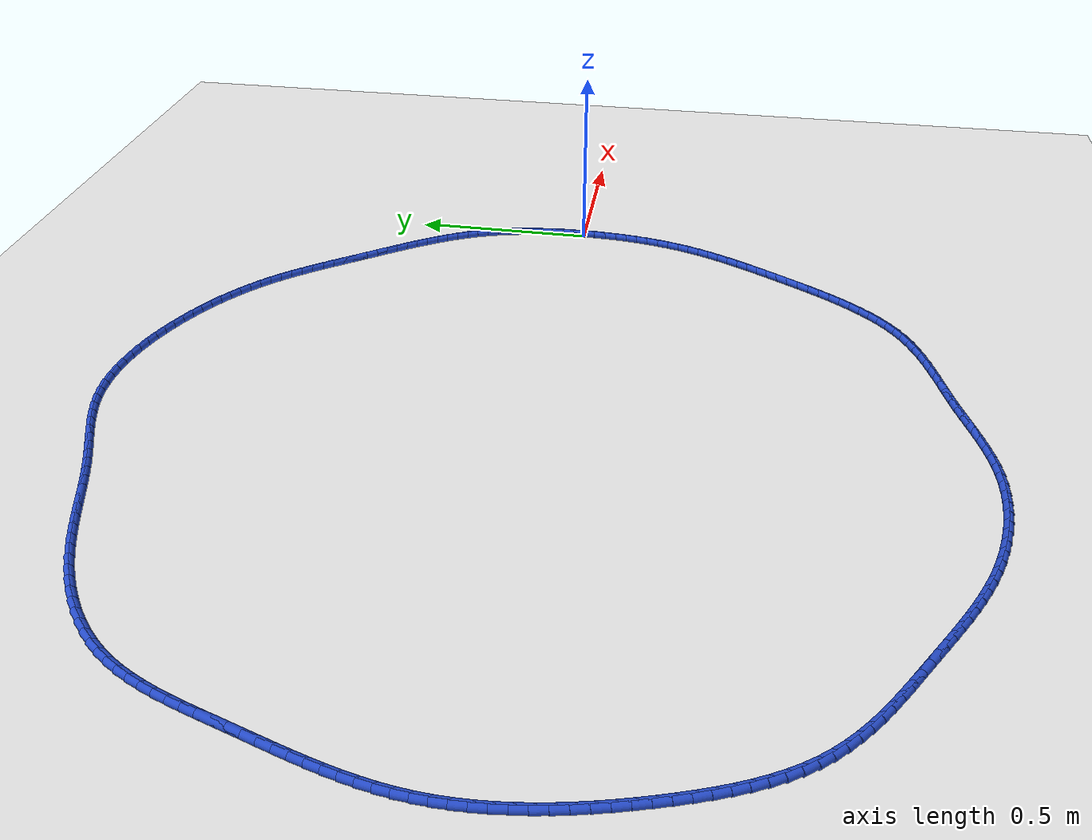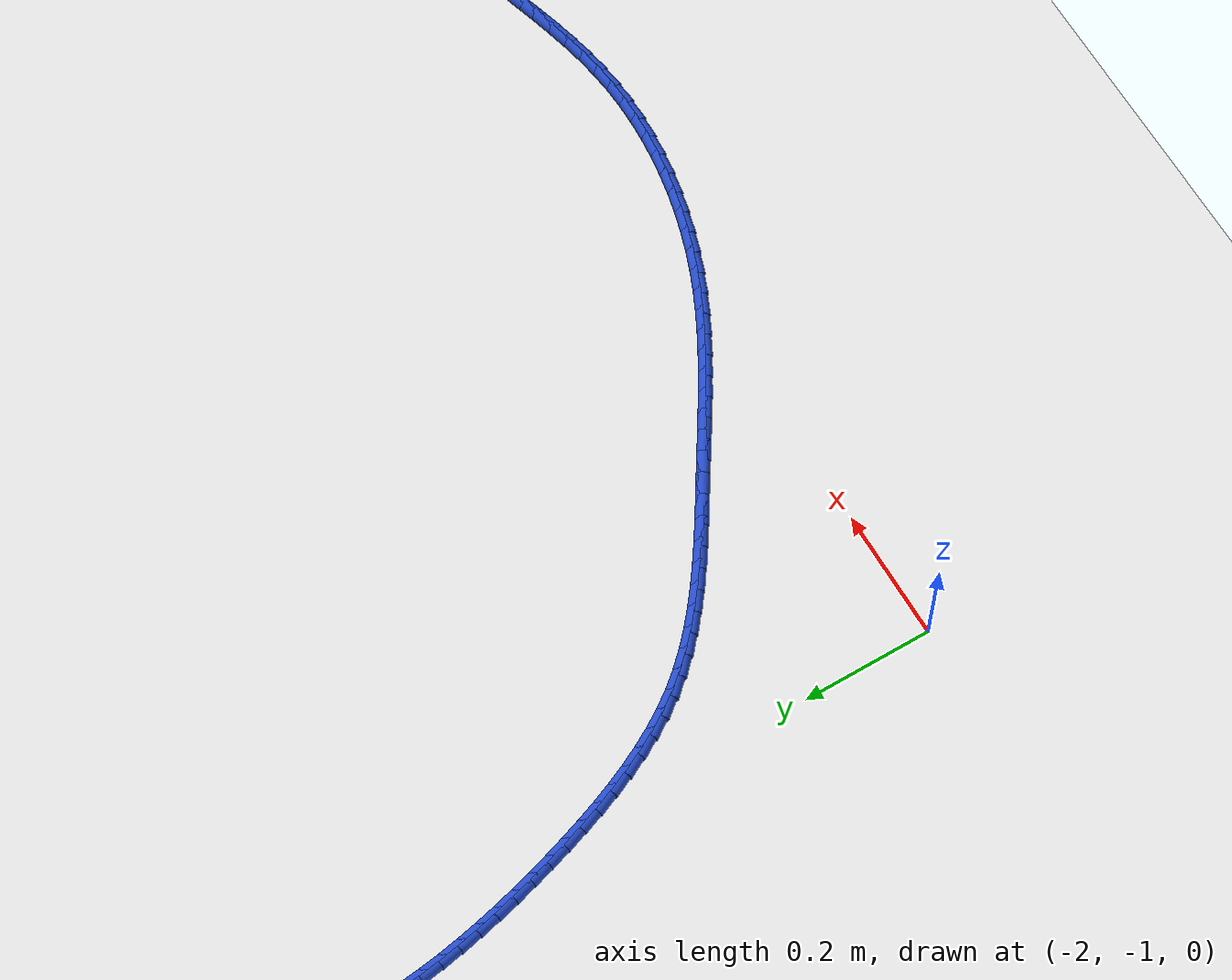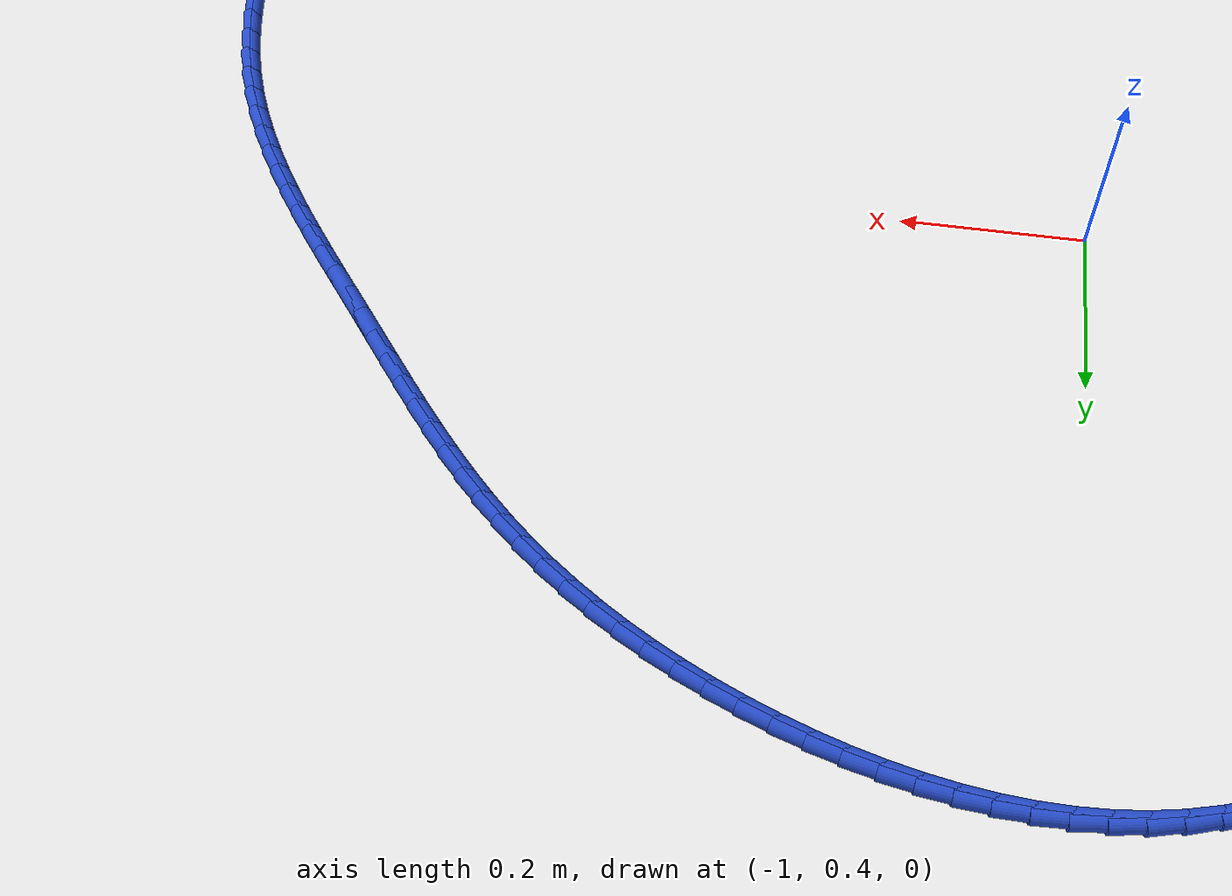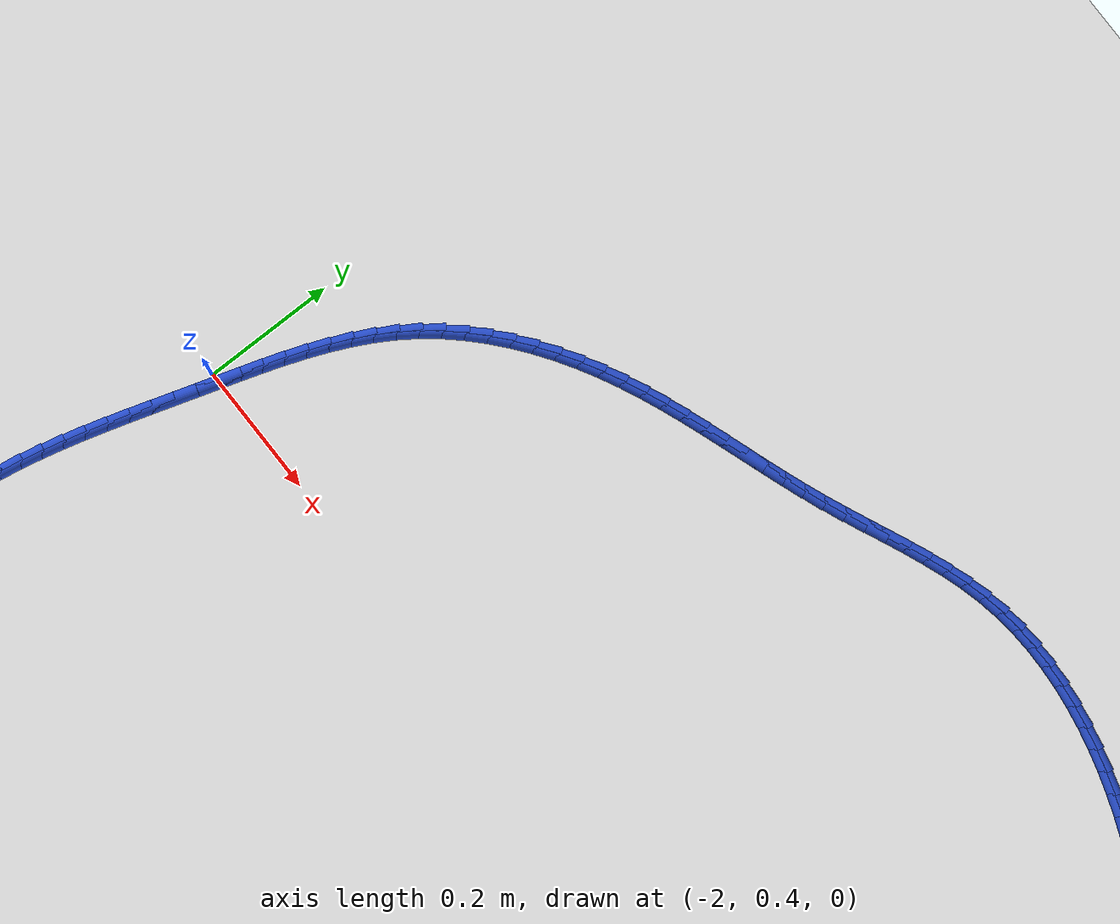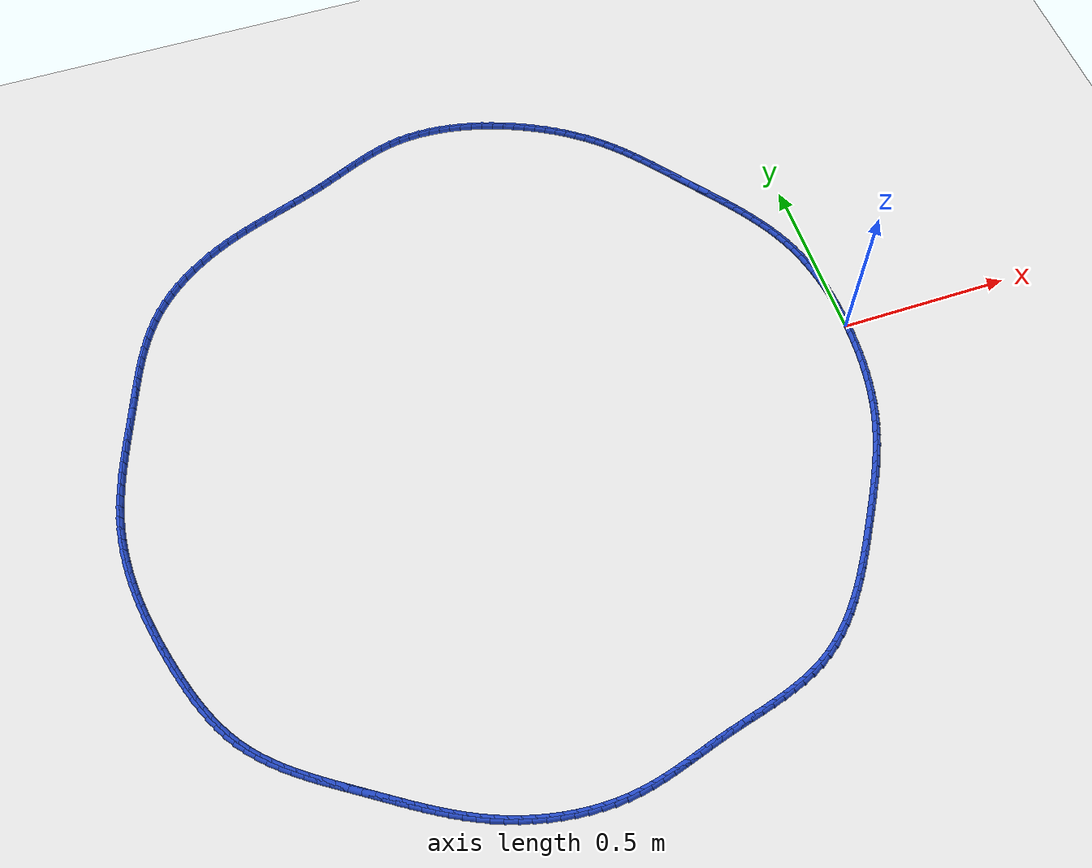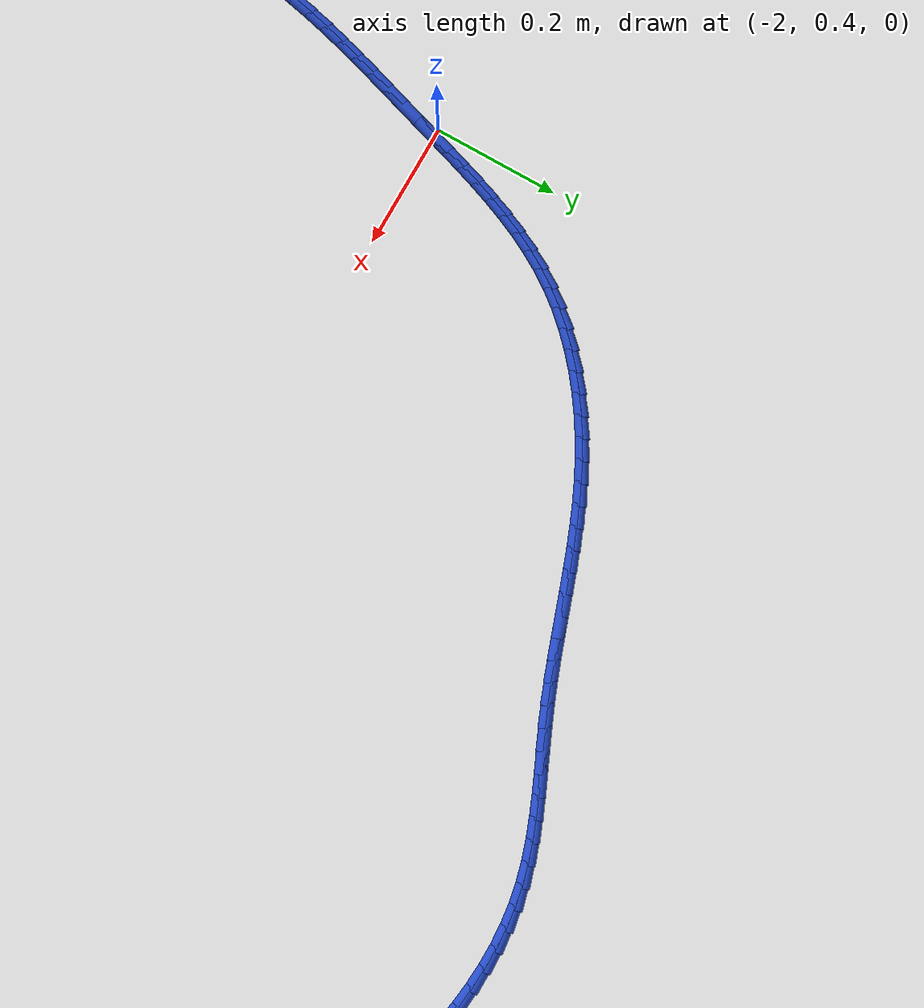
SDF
<sdf version="1.6">
 <world name="default">
  <light name="sun" type="directional">
   <pose>0 0 10 0 -0 0</pose>
   <diffuse>0.8 0.8 0.8 1</diffuse>
   <specular>0.2 0.2 0.2 1</specular>
   <attenuation>
    <range>1000</range>
    <constant>0.9</constant>
    <linear>0.01</linear>
    <quadratic>0.001</quadratic>
   </attenuation>
   <direction>-0.5 0.1 -0.9</direction>
  </light>
  <model name="ground_plane">
   <static>1</static>
   <link name="link">
    <collision name="collision">
     <geometry><plane><normal>0 0 1</normal><size>100 100</size></plane></geometry>
     <surface><friction><ode><mu>100</mu><mu2>50</mu2></ode></friction></surface>
    </collision>
    <visual name="visual">
     <cast_shadows>0</cast_shadows>
     <geometry><plane><normal>0 0 1</normal><size>100 100</size></plane></geometry>
     <material>
      <script><uri>file://media/materials/scripts/gazebo.material</uri><name>Gazebo/WhiteGlow</name></script>
     </material>
    </visual>
   </link>
  </model>
  <gravity>0 0 -9.8</gravity>
  <magnetic_field>6e-06 2.3e-05 -4.2e-05</magnetic_field>
  <atmosphere type="adiabatic"/>
  <physics name="default_physics" default="0" type="ode">
   <max_step_size>0.001</max_step_size>
   <real_time_factor>1</real_time_factor>
   <real_time_update_rate>1000</real_time_update_rate>
  </physics>
  <scene><ambient>0.4 0.4 0.4 1</ambient><background>0.7 0.7 0.7 1</background><shadows>1</shadows></scene>
  <spherical_coordinates>
   <surface_model>EARTH_WGS84</surface_model>
   <latitude_deg>0</latitude_deg>
   <longitude_deg>0</longitude_deg>
   <elevation>0</elevation>
   <heading_deg>0</heading_deg>
  </spherical_coordinates>
  <model name="line">
   <link name="link_0">
    <pose>-1.474514954580286e-17 -6.245004513516506e-17 0.01 0 1.57 -1.566864676867693</pose>
    <collision name="collision">
     <geometry><cylinder><radius>0.01</radius><length>0.08</length></cylinder></geometry>
    </collision>
    <visual name="visual">
     <material>
      <script><name>Gazebo/Blue</name><uri>file://media/materials/scripts/gazebo.material</uri></script>
     </material>
     <geometry><cylinder><radius>0.01</radius><length>0.08</length></cylinder></geometry>
    </visual>
   </link>
   <link name="link_1">
    <pose>-0.00013139709490835573 0.03342017226882433 0.01 0 1.57 -1.538017861132489</pose>
    <collision name="collision">
     <geometry><cylinder><radius>0.01</radius><length>0.08</length></cylinder></geometry>
    </collision>
    <visual name="visual">
     <material>
      <script><name>Gazebo/Blue</name><uri>file://media/materials/scripts/gazebo.material</uri></script>
     </material>
     <geometry><cylinder><radius>0.01</radius><length>0.08</length></cylinder></geometry>
    </visual>
   </link>
   <link name="link_2">
    <pose>-0.0012262345714651086 0.06680932940006966 0.01 0 1.57 -1.5065309027381384</pose>
    <collision name="collision">
     <geometry><cylinder><radius>0.01</radius><length>0.08</length></cylinder></geometry>
    </collision>
    <visual name="visual">
     <material>
      <script><name>Gazebo/Blue</name><uri>file://media/materials/scripts/gazebo.material</uri></script>
     </material>
     <geometry><cylinder><radius>0.01</radius><length>0.08</length></cylinder></geometry>
    </visual>
   </link>
   <link name="link_3">
    <pose>-0.003367712617615145 0.10008584055856341 0.01 0 1.57 -1.4722322931732916</pose>
    <collision name="collision">
     <geometry><cylinder><radius>0.01</radius><length>0.08</length></cylinder></geometry>
    </collision>
    <visual name="visual">
     <material>
      <script><name>Gazebo/Blue</name><uri>file://media/materials/scripts/gazebo.material</uri></script>
     </material>
     <geometry><cylinder><radius>0.01</radius><length>0.08</length></cylinder></geometry>
    </visual>
   </link>
   <link name="link_4">
    <pose>-0.0066390314213033465 0.1331680749091331 0.01 0 1.57 -1.4349463374511788</pose>
    <collision name="collision">
     <geometry><cylinder><radius>0.01</radius><length>0.08</length></cylinder></geometry>
    </collision>
    <visual name="visual">
     <material>
      <script><name>Gazebo/Blue</name><uri>file://media/materials/scripts/gazebo.material</uri></script>
     </material>
     <geometry><cylinder><radius>0.01</radius><length>0.08</length></cylinder></geometry>
    </visual>
   </link>
   <link name="link_5">
    <pose>-0.01112339117047459 0.16597440161660623 0.01 0 1.57 -1.3945004085183659</pose>
    <collision name="collision">
     <geometry><cylinder><radius>0.01</radius><length>0.08</length></cylinder></geometry>
    </collision>
    <visual name="visual">
     <material>
      <script><name>Gazebo/Blue</name><uri>file://media/materials/scripts/gazebo.material</uri></script>
     </material>
     <geometry><cylinder><radius>0.01</radius><length>0.08</length></cylinder></geometry>
    </visual>
   </link>
   <link name="link_6">
    <pose>-0.016903992053073746 0.1984231898458103 0.01 0 1.57 -1.3507347471098634</pose>
    <collision name="collision">
     <geometry><cylinder><radius>0.01</radius><length>0.08</length></cylinder></geometry>
    </collision>
    <visual name="visual">
     <material>
      <script><name>Gazebo/Blue</name><uri>file://media/materials/scripts/gazebo.material</uri></script>
     </material>
     <geometry><cylinder><radius>0.01</radius><length>0.08</length></cylinder></geometry>
    </visual>
   </link>
   <link name="link_7">
    <pose>-0.024064034257045716 0.23043280876157285 0.01 0 1.57 -1.3035152125114116</pose>
    <collision name="collision">
     <geometry><cylinder><radius>0.01</radius><length>0.08</length></cylinder></geometry>
    </collision>
    <visual name="visual">
     <material>
      <script><name>Gazebo/Blue</name><uri>file://media/materials/scripts/gazebo.material</uri></script>
     </material>
     <geometry><cylinder><radius>0.01</radius><length>0.08</length></cylinder></geometry>
    </visual>
   </link>
   <link name="link_8">
    <pose>-0.032686717970335344 0.2619216275287214 0.01 0 1.57 -1.2527491504995119</pose>
    <collision name="collision">
     <geometry><cylinder><radius>0.01</radius><length>0.08</length></cylinder></geometry>
    </collision>
    <visual name="visual">
     <material>
      <script><name>Gazebo/Blue</name><uri>file://media/materials/scripts/gazebo.material</uri></script>
     </material>
     <geometry><cylinder><radius>0.01</radius><length>0.08</length></cylinder></geometry>
    </visual>
   </link>
   <link name="link_9">
    <pose>-0.04285524338088752 0.2928080153120832 0.01 0 1.57 -1.1985505220806716</pose>
    <collision name="collision">
     <geometry><cylinder><radius>0.01</radius><length>0.08</length></cylinder></geometry>
    </collision>
    <visual name="visual">
     <material>
      <script><name>Gazebo/Blue</name><uri>file://media/materials/scripts/gazebo.material</uri></script>
     </material>
     <geometry><cylinder><radius>0.01</radius><length>0.08</length></cylinder></geometry>
    </visual>
   </link>
   <link name="link_10">
    <pose>-0.05464869573752489 0.323012856468047 0.01 0 1.57 -1.1449753626782009</pose>
    <collision name="collision">
     <geometry><cylinder><radius>0.01</radius><length>0.08</length></cylinder></geometry>
    </collision>
    <visual name="visual">
     <material>
      <script><name>Gazebo/Blue</name><uri>file://media/materials/scripts/gazebo.material</uri></script>
     </material>
     <geometry><cylinder><radius>0.01</radius><length>0.08</length></cylinder></geometry>
    </visual>
   </link>
   <link name="link_11">
    <pose>-0.06803467725487487 0.35252517759726243 0.01 0 1.57 -1.0966031735636597</pose>
    <collision name="collision">
     <geometry><cylinder><radius>0.01</radius><length>0.08</length></cylinder></geometry>
    </collision>
    <visual name="visual">
     <material>
      <script><name>Gazebo/Blue</name><uri>file://media/materials/scripts/gazebo.material</uri></script>
     </material>
     <geometry><cylinder><radius>0.01</radius><length>0.08</length></cylinder></geometry>
    </visual>
   </link>
   <link name="link_12">
    <pose>-0.08285906238558022 0.38140840947273086 0.01 0 1.57 -1.0538123843574</pose>
    <collision name="collision">
     <geometry><cylinder><radius>0.01</radius><length>0.08</length></cylinder></geometry>
    </collision>
    <visual name="visual">
     <material>
      <script><name>Gazebo/Blue</name><uri>file://media/materials/scripts/gazebo.material</uri></script>
     </material>
     <geometry><cylinder><radius>0.01</radius><length>0.08</length></cylinder></geometry>
    </visual>
   </link>
   <link name="link_13">
    <pose>-0.09896155673196752 0.4097297534797995 0.01 0 1.57 -1.016637372810215</pose>
    <collision name="collision">
     <geometry><cylinder><radius>0.01</radius><length>0.08</length></cylinder></geometry>
    </collision>
    <visual name="visual">
     <material>
      <script><name>Gazebo/Blue</name><uri>file://media/materials/scripts/gazebo.material</uri></script>
     </material>
     <geometry><cylinder><radius>0.01</radius><length>0.08</length></cylinder></geometry>
    </visual>
   </link>
   <link name="link_14">
    <pose>-0.1161818658963633 0.43755641100381526 0.01 0 1.57 -0.9850277895602266</pose>
    <collision name="collision">
     <geometry><cylinder><radius>0.01</radius><length>0.08</length></cylinder></geometry>
    </collision>
    <visual name="visual">
     <material>
      <script><name>Gazebo/Blue</name><uri>file://media/materials/scripts/gazebo.material</uri></script>
     </material>
     <geometry><cylinder><radius>0.01</radius><length>0.08</length></cylinder></geometry>
    </visual>
   </link>
   <link name="link_15">
    <pose>-0.134359695481094 0.464955583430125 0.01 0 1.57 -0.9588840580511969</pose>
    <collision name="collision">
     <geometry><cylinder><radius>0.01</radius><length>0.08</length></cylinder></geometry>
    </collision>
    <visual name="visual">
     <material>
      <script><name>Gazebo/Blue</name><uri>file://media/materials/scripts/gazebo.material</uri></script>
     </material>
     <geometry><cylinder><radius>0.01</radius><length>0.08</length></cylinder></geometry>
    </visual>
   </link>
   <link name="link_16">
    <pose>-0.15333475108848643 0.4919944721440762 0.01 0 1.57 -0.9380864949233623</pose>
    <collision name="collision">
     <geometry><cylinder><radius>0.01</radius><length>0.08</length></cylinder></geometry>
    </collision>
    <visual name="visual">
     <material>
      <script><name>Gazebo/Blue</name><uri>file://media/materials/scripts/gazebo.material</uri></script>
     </material>
     <geometry><cylinder><radius>0.01</radius><length>0.08</length></cylinder></geometry>
    </visual>
   </link>
   <link name="link_17">
    <pose>-0.17294673832086693 0.5187402785310158 0.01 0 1.57 -0.9225177211802233</pose>
    <collision name="collision">
     <geometry><cylinder><radius>0.01</radius><length>0.08</length></cylinder></geometry>
    </collision>
    <visual name="visual">
     <material>
      <script><name>Gazebo/Blue</name><uri>file://media/materials/scripts/gazebo.material</uri></script>
     </material>
     <geometry><cylinder><radius>0.01</radius><length>0.08</length></cylinder></geometry>
    </visual>
   </link>
   <link name="link_18">
    <pose>-0.19303536278056205 0.5452602039762905 0.01 0 1.57 -0.9120789843671948</pose>
    <collision name="collision">
     <geometry><cylinder><radius>0.01</radius><length>0.08</length></cylinder></geometry>
    </collision>
    <visual name="visual">
     <material>
      <script><name>Gazebo/Blue</name><uri>file://media/materials/scripts/gazebo.material</uri></script>
     </material>
     <geometry><cylinder><radius>0.01</radius><length>0.08</length></cylinder></geometry>
    </visual>
   </link>
   <link name="link_19">
    <pose>-0.21344033006989852 0.5716214498652478 0.01 0 1.57 -0.9067013673730009</pose>
    <collision name="collision">
     <geometry><cylinder><radius>0.01</radius><length>0.08</length></cylinder></geometry>
    </collision>
    <visual name="visual">
     <material>
      <script><name>Gazebo/Blue</name><uri>file://media/materials/scripts/gazebo.material</uri></script>
     </material>
     <geometry><cylinder><radius>0.01</radius><length>0.08</length></cylinder></geometry>
    </visual>
   </link>
   <link name="link_20">
    <pose>-0.23400134579120274 0.5978912175832344 0.01 0 1.57 -0.9063528339569071</pose>
    <collision name="collision">
     <geometry><cylinder><radius>0.01</radius><length>0.08</length></cylinder></geometry>
    </collision>
    <visual name="visual">
     <material>
      <script><name>Gazebo/Blue</name><uri>file://media/materials/scripts/gazebo.material</uri></script>
     </material>
     <geometry><cylinder><radius>0.01</radius><length>0.08</length></cylinder></geometry>
    </visual>
   </link>
   <link name="link_21">
    <pose>-0.25455811554680136 0.6241367085155975 0.01 0 1.57 -0.90967437598894</pose>
    <collision name="collision">
     <geometry><cylinder><radius>0.01</radius><length>0.08</length></cylinder></geometry>
    </collision>
    <visual name="visual">
     <material>
      <script><name>Gazebo/Blue</name><uri>file://media/materials/scripts/gazebo.material</uri></script>
     </material>
     <geometry><cylinder><radius>0.01</radius><length>0.08</length></cylinder></geometry>
    </visual>
   </link>
   <link name="link_22">
    <pose>-0.2749888605382059 0.6504005393528542 0.01 0 1.57 -0.9100517620196373</pose>
    <collision name="collision">
     <geometry><cylinder><radius>0.01</radius><length>0.08</length></cylinder></geometry>
    </collision>
    <visual name="visual">
     <material>
      <script><name>Gazebo/Blue</name><uri>file://media/materials/scripts/gazebo.material</uri></script>
     </material>
     <geometry><cylinder><radius>0.01</radius><length>0.08</length></cylinder></geometry>
    </visual>
   </link>
   <link name="link_23">
    <pose>-0.2953584674703887 0.6766061772841523 0.01 0 1.57 -0.9054481592668284</pose>
    <collision name="collision">
     <geometry><cylinder><radius>0.01</radius><length>0.08</length></cylinder></geometry>
    </collision>
    <visual name="visual">
     <material>
      <script><name>Gazebo/Blue</name><uri>file://media/materials/scripts/gazebo.material</uri></script>
     </material>
     <geometry><cylinder><radius>0.01</radius><length>0.08</length></cylinder></geometry>
    </visual>
   </link>
   <link name="link_24">
    <pose>-0.3157882947583612 0.7026410433306656 0.01 0 1.57 -0.895813618350035</pose>
    <collision name="collision">
     <geometry><cylinder><radius>0.01</radius><length>0.08</length></cylinder></geometry>
    </collision>
    <visual name="visual">
     <material>
      <script><name>Gazebo/Blue</name><uri>file://media/materials/scripts/gazebo.material</uri></script>
     </material>
     <geometry><cylinder><radius>0.01</radius><length>0.08</length></cylinder></geometry>
    </visual>
   </link>
   <link name="link_25">
    <pose>-0.3363997130292456 0.7283925507185185 0.01 0 1.57 -0.8810891884011294</pose>
    <collision name="collision">
     <geometry><cylinder><radius>0.01</radius><length>0.08</length></cylinder></geometry>
    </collision>
    <visual name="visual">
     <material>
      <script><name>Gazebo/Blue</name><uri>file://media/materials/scripts/gazebo.material</uri></script>
     </material>
     <geometry><cylinder><radius>0.01</radius><length>0.08</length></cylinder></geometry>
    </visual>
   </link>
   <link name="link_26">
    <pose>-0.35731409291016397 0.7537481126738343 0.01 0 1.57 -0.8612136206077178</pose>
    <collision name="collision">
     <geometry><cylinder><radius>0.01</radius><length>0.08</length></cylinder></geometry>
    </collision>
    <visual name="visual">
     <material>
      <script><name>Gazebo/Blue</name><uri>file://media/materials/scripts/gazebo.material</uri></script>
     </material>
     <geometry><cylinder><radius>0.01</radius><length>0.08</length></cylinder></geometry>
    </visual>
   </link>
   <link name="link_27">
    <pose>-0.37865280502823895 0.7785951424227378 0.01 0 1.57 -0.8361348743832212</pose>
    <collision name="collision">
     <geometry><cylinder><radius>0.01</radius><length>0.08</length></cylinder></geometry>
    </collision>
    <visual name="visual">
     <material>
      <script><name>Gazebo/Blue</name><uri>file://media/materials/scripts/gazebo.material</uri></script>
     </material>
     <geometry><cylinder><radius>0.01</radius><length>0.08</length></cylinder></geometry>
    </visual>
   </link>
   <link name="link_28">
    <pose>-0.4005372200105929 0.802821053191353 0.01 0 1.57 -0.8058262743873813</pose>
    <collision name="collision">
     <geometry><cylinder><radius>0.01</radius><length>0.08</length></cylinder></geometry>
    </collision>
    <visual name="visual">
     <material>
      <script><name>Gazebo/Blue</name><uri>file://media/materials/scripts/gazebo.material</uri></script>
     </material>
     <geometry><cylinder><radius>0.01</radius><length>0.08</length></cylinder></geometry>
    </visual>
   </link>
   <link name="link_29">
    <pose>-0.42308870848434743 0.8263132582058028 0.01 0 1.57 -0.7703072714142016</pose>
    <collision name="collision">
     <geometry><cylinder><radius>0.01</radius><length>0.08</length></cylinder></geometry>
    </collision>
    <visual name="visual">
     <material>
      <script><name>Gazebo/Blue</name><uri>file://media/materials/scripts/gazebo.material</uri></script>
     </material>
     <geometry><cylinder><radius>0.01</radius><length>0.08</length></cylinder></geometry>
    </visual>
   </link>
   <link name="link_30">
    <pose>-0.44642864107662567 0.8489591706922126 0.01 0 1.57 -0.7299325000089637</pose>
    <collision name="collision">
     <geometry><cylinder><radius>0.01</radius><length>0.08</length></cylinder></geometry>
    </collision>
    <visual name="visual">
     <material>
      <script><name>Gazebo/Blue</name><uri>file://media/materials/scripts/gazebo.material</uri></script>
     </material>
     <geometry><cylinder><radius>0.01</radius><length>0.08</length></cylinder></geometry>
    </visual>
   </link>
   <link name="link_31">
    <pose>-0.4706711245822668 0.8706512474147835 0.01 0 1.57 -0.68808438988185</pose>
    <collision name="collision">
     <geometry><cylinder><radius>0.01</radius><length>0.08</length></cylinder></geometry>
    </collision>
    <visual name="visual">
     <material>
      <script><name>Gazebo/Blue</name><uri>file://media/materials/scripts/gazebo.material</uri></script>
     </material>
     <geometry><cylinder><radius>0.01</radius><length>0.08</length></cylinder></geometry>
    </visual>
   </link>
   <link name="link_32">
    <pose>-0.49584100168224354 0.8913439243987712 0.01 0 1.57 -0.6469970846527484</pose>
    <collision name="collision">
     <geometry><cylinder><radius>0.01</radius><length>0.08</length></cylinder></geometry>
    </collision>
    <visual name="visual">
     <material>
      <script><name>Gazebo/Blue</name><uri>file://media/materials/scripts/gazebo.material</uri></script>
     </material>
     <geometry><cylinder><radius>0.01</radius><length>0.08</length></cylinder></geometry>
    </visual>
   </link>
   <link name="link_33">
    <pose>-0.5219031497045087 0.9110332737548389 0.01 0 1.57 -0.6067290212405997</pose>
    <collision name="collision">
     <geometry><cylinder><radius>0.01</radius><length>0.08</length></cylinder></geometry>
    </collision>
    <visual name="visual">
     <material>
      <script><name>Gazebo/Blue</name><uri>file://media/materials/scripts/gazebo.material</uri></script>
     </material>
     <geometry><cylinder><radius>0.01</radius><length>0.08</length></cylinder></geometry>
    </visual>
   </link>
   <link name="link_34">
    <pose>-0.5488213341924688 0.9297161395453536 0.01 0 1.57 -0.567287908410215</pose>
    <collision name="collision">
     <geometry><cylinder><radius>0.01</radius><length>0.08</length></cylinder></geometry>
    </collision>
    <visual name="visual">
     <material>
      <script><name>Gazebo/Blue</name><uri>file://media/materials/scripts/gazebo.material</uri></script>
     </material>
     <geometry><cylinder><radius>0.01</radius><length>0.08</length></cylinder></geometry>
    </visual>
   </link>
   <link name="link_35">
    <pose>-0.57655932068953 0.947389365832681 0.01 0 1.57 -0.5286721881044404</pose>
    <collision name="collision">
     <geometry><cylinder><radius>0.01</radius><length>0.08</length></cylinder></geometry>
    </collision>
    <visual name="visual">
     <material>
      <script><name>Gazebo/Blue</name><uri>file://media/materials/scripts/gazebo.material</uri></script>
     </material>
     <geometry><cylinder><radius>0.01</radius><length>0.08</length></cylinder></geometry>
    </visual>
   </link>
   <link name="link_36">
    <pose>-0.6050808747390986 0.9640497966791872 0.01 0 1.57 -0.4908720810295509</pose>
    <collision name="collision">
     <geometry><cylinder><radius>0.01</radius><length>0.08</length></cylinder></geometry>
    </collision>
    <visual name="visual">
     <material>
      <script><name>Gazebo/Blue</name><uri>file://media/materials/scripts/gazebo.material</uri></script>
     </material>
     <geometry><cylinder><radius>0.01</radius><length>0.08</length></cylinder></geometry>
    </visual>
   </link>
   <link name="link_37">
    <pose>-0.6343497618845811 0.9796942761472387 0.01 0 1.57 -0.4538706446735768</pose>
    <collision name="collision">
     <geometry><cylinder><radius>0.01</radius><length>0.08</length></cylinder></geometry>
    </collision>
    <visual name="visual">
     <material>
      <script><name>Gazebo/Blue</name><uri>file://media/materials/scripts/gazebo.material</uri></script>
     </material>
     <geometry><cylinder><radius>0.01</radius><length>0.08</length></cylinder></geometry>
    </visual>
   </link>
   <link name="link_38">
    <pose>-0.6643297476693841 0.9943196482992017 0.01 0 1.57 -0.4176448072118218</pose>
    <collision name="collision">
     <geometry><cylinder><radius>0.01</radius><length>0.08</length></cylinder></geometry>
    </collision>
    <visual name="visual">
     <material>
      <script><name>Gazebo/Blue</name><uri>file://media/materials/scripts/gazebo.material</uri></script>
     </material>
     <geometry><cylinder><radius>0.01</radius><length>0.08</length></cylinder></geometry>
    </visual>
   </link>
   <link name="link_39">
    <pose>-0.6949845976369133 1.0079227571974423 0.01 0 1.57 -0.38186531664303963</pose>
    <collision name="collision">
     <geometry><cylinder><radius>0.01</radius><length>0.08</length></cylinder></geometry>
    </collision>
    <visual name="visual">
     <material>
      <script><name>Gazebo/Blue</name><uri>file://media/materials/scripts/gazebo.material</uri></script>
     </material>
     <geometry><cylinder><radius>0.01</radius><length>0.08</length></cylinder></geometry>
    </visual>
   </link>
   <link name="link_40">
    <pose>-0.7262699692889628 1.020486250027727 0.01 0 1.57 -0.3448632830701141</pose>
    <collision name="collision">
     <geometry><cylinder><radius>0.01</radius><length>0.08</length></cylinder></geometry>
    </collision>
    <visual name="visual">
     <material>
      <script><name>Gazebo/Blue</name><uri>file://media/materials/scripts/gazebo.material</uri></script>
     </material>
     <geometry><cylinder><radius>0.01</radius><length>0.08</length></cylinder></geometry>
    </visual>
   </link>
   <link name="link_41">
    <pose>-0.7581000731409825 1.0319202018580838 0.01 0 1.57 -0.30585035486515677</pose>
    <collision name="collision">
     <geometry><cylinder><radius>0.01</radius><length>0.08</length></cylinder></geometry>
    </collision>
    <visual name="visual">
     <material>
      <script><name>Gazebo/Blue</name><uri>file://media/materials/scripts/gazebo.material</uri></script>
     </material>
     <geometry><cylinder><radius>0.01</radius><length>0.08</length></cylinder></geometry>
    </visual>
   </link>
   <link name="link_42">
    <pose>-0.7903759108145719 1.0421115594790884 0.01 0 1.57 -0.26450042342660635</pose>
    <collision name="collision">
     <geometry><cylinder><radius>0.01</radius><length>0.08</length></cylinder></geometry>
    </collision>
    <visual name="visual">
     <material>
      <script><name>Gazebo/Blue</name><uri>file://media/materials/scripts/gazebo.material</uri></script>
     </material>
     <geometry><cylinder><radius>0.01</radius><length>0.08</length></cylinder></geometry>
    </visual>
   </link>
   <link name="link_43">
    <pose>-0.822998478279847 1.0509472597857805 0.01 0 1.57 -0.22047928839159955</pose>
    <collision name="collision">
     <geometry><cylinder><radius>0.01</radius><length>0.08</length></cylinder></geometry>
    </collision>
    <visual name="visual">
     <material>
      <script><name>Gazebo/Blue</name><uri>file://media/materials/scripts/gazebo.material</uri></script>
     </material>
     <geometry><cylinder><radius>0.01</radius><length>0.08</length></cylinder></geometry>
    </visual>
   </link>
   <link name="link_44">
    <pose>-0.855868771506923 1.058314239673199 0.01 0 1.57 -0.17344750182670687</pose>
    <collision name="collision">
     <geometry><cylinder><radius>0.01</radius><length>0.08</length></cylinder></geometry>
    </collision>
    <visual name="visual">
     <material>
      <script><name>Gazebo/Blue</name><uri>file://media/materials/scripts/gazebo.material</uri></script>
     </material>
     <geometry><cylinder><radius>0.01</radius><length>0.08</length></cylinder></geometry>
    </visual>
   </link>
   <link name="link_45">
    <pose>-0.8888877864659157 1.0640994360363836 0.01 0 1.57 -0.12306726998541412</pose>
    <collision name="collision">
     <geometry><cylinder><radius>0.01</radius><length>0.08</length></cylinder></geometry>
    </collision>
    <visual name="visual">
     <material>
      <script><name>Gazebo/Blue</name><uri>file://media/materials/scripts/gazebo.material</uri></script>
     </material>
     <geometry><cylinder><radius>0.01</radius><length>0.08</length></cylinder></geometry>
    </visual>
   </link>
   <link name="link_46">
    <pose>-0.9219565191269404 1.0681897857703726 0.01 0 1.57 -0.06901433440851065</pose>
    <collision name="collision">
     <geometry><cylinder><radius>0.01</radius><length>0.08</length></cylinder></geometry>
    </collision>
    <visual name="visual">
     <material>
      <script><name>Gazebo/Blue</name><uri>file://media/materials/scripts/gazebo.material</uri></script>
     </material>
     <geometry><cylinder><radius>0.01</radius><length>0.08</length></cylinder></geometry>
    </visual>
   </link>
   <link name="link_47">
    <pose>-0.9549759654601131 1.0704722257702062 0.01 0 1.57 -0.010996041398290225</pose>
    <collision name="collision">
     <geometry><cylinder><radius>0.01</radius><length>0.08</length></cylinder></geometry>
    </collision>
    <visual name="visual">
     <material>
      <script><name>Gazebo/Blue</name><uri>file://media/materials/scripts/gazebo.material</uri></script>
     </material>
     <geometry><cylinder><radius>0.01</radius><length>0.08</length></cylinder></geometry>
    </visual>
   </link>
   <link name="link_48">
    <pose>-0.9878471214355489 1.0708336929309232 0.01 0 1.57 0.05122341733824503</pose>
    <collision name="collision">
     <geometry><cylinder><radius>0.01</radius><length>0.08</length></cylinder></geometry>
    </collision>
    <visual name="visual">
     <material>
      <script><name>Gazebo/Blue</name><uri>file://media/materials/scripts/gazebo.material</uri></script>
     </material>
     <geometry><cylinder><radius>0.01</radius><length>0.08</length></cylinder></geometry>
    </visual>
   </link>
   <link name="link_49">
    <pose>-1.0204709830233634 1.0691611241475625 0.01 0 1.57 0.11779036829307583</pose>
    <collision name="collision">
     <geometry><cylinder><radius>0.01</radius><length>0.08</length></cylinder></geometry>
    </collision>
    <visual name="visual">
     <material>
      <script><name>Gazebo/Blue</name><uri>file://media/materials/scripts/gazebo.material</uri></script>
     </material>
     <geometry><cylinder><radius>0.01</radius><length>0.08</length></cylinder></geometry>
    </visual>
   </link>
   <link name="link_50">
    <pose>-1.0527485461936725 1.0653414563151642 0.01 0 1.57 0.18861127148207724</pose>
    <collision name="collision">
     <geometry><cylinder><radius>0.01</radius><length>0.08</length></cylinder></geometry>
    </collision>
    <visual name="visual">
     <material>
      <script><name>Gazebo/Blue</name><uri>file://media/materials/scripts/gazebo.material</uri></script>
     </material>
     <geometry><cylinder><radius>0.01</radius><length>0.08</length></cylinder></geometry>
    </visual>
   </link>
   <link name="link_51">
    <pose>-1.0845821027197131 1.059265062975896 0.01 0 1.57 0.25732935869336016</pose>
    <collision name="collision">
     <geometry><cylinder><radius>0.01</radius><length>0.08</length></cylinder></geometry>
    </collision>
    <visual name="visual">
     <material>
      <script><name>Gazebo/Blue</name><uri>file://media/materials/scripts/gazebo.material</uri></script>
     </material>
     <geometry><cylinder><radius>0.01</radius><length>0.08</length></cylinder></geometry>
    </visual>
   </link>
   <link name="link_52">
    <pose>-1.115945244497374 1.0510114153502563 0.01 0 1.57 0.314274118821379</pose>
    <collision name="collision">
     <geometry><cylinder><radius>0.01</radius><length>0.08</length></cylinder></geometry>
    </collision>
    <visual name="visual">
     <material>
      <script><name>Gazebo/Blue</name><uri>file://media/materials/scripts/gazebo.material</uri></script>
     </material>
     <geometry><cylinder><radius>0.01</radius><length>0.08</length></cylinder></geometry>
    </visual>
   </link>
   <link name="link_53">
    <pose>-1.1469185223014469 1.040943654236364 0.01 0 1.57 0.3585739039393243</pose>
    <collision name="collision">
     <geometry><cylinder><radius>0.01</radius><length>0.08</length></cylinder></geometry>
    </collision>
    <visual name="visual">
     <material>
      <script><name>Gazebo/Blue</name><uri>file://media/materials/scripts/gazebo.material</uri></script>
     </material>
     <geometry><cylinder><radius>0.01</radius><length>0.08</length></cylinder></geometry>
    </visual>
   </link>
   <link name="link_54">
    <pose>-1.1775912842163134 1.0294482521007482 0.01 0 1.57 0.390426303165997</pose>
    <collision name="collision">
     <geometry><cylinder><radius>0.01</radius><length>0.08</length></cylinder></geometry>
    </collision>
    <visual name="visual">
     <material>
      <script><name>Gazebo/Blue</name><uri>file://media/materials/scripts/gazebo.material</uri></script>
     </material>
     <geometry><cylinder><radius>0.01</radius><length>0.08</length></cylinder></geometry>
    </visual>
   </link>
   <link name="link_55">
    <pose>-1.2080528783263569 1.0169116814099375 0.01 0 1.57 0.4101290182392701</pose>
    <collision name="collision">
     <geometry><cylinder><radius>0.01</radius><length>0.08</length></cylinder></geometry>
    </collision>
    <visual name="visual">
     <material>
      <script><name>Gazebo/Blue</name><uri>file://media/materials/scripts/gazebo.material</uri></script>
     </material>
     <geometry><cylinder><radius>0.01</radius><length>0.08</length></cylinder></geometry>
    </visual>
   </link>
   <link name="link_56">
    <pose>-1.2383926527159594 1.0037204146304604 0.01 0 1.57 0.41793713932090404</pose>
    <collision name="collision">
     <geometry><cylinder><radius>0.01</radius><length>0.08</length></cylinder></geometry>
    </collision>
    <visual name="visual">
     <material>
      <script><name>Gazebo/Blue</name><uri>file://media/materials/scripts/gazebo.material</uri></script>
     </material>
     <geometry><cylinder><radius>0.01</radius><length>0.08</length></cylinder></geometry>
    </visual>
   </link>
   <link name="link_57">
    <pose>-1.2686999554695035 0.9902609242288455 0.01 0 1.57 0.413982584713164</pose>
    <collision name="collision">
     <geometry><cylinder><radius>0.01</radius><length>0.08</length></cylinder></geometry>
    </collision>
    <visual name="visual">
     <material>
      <script><name>Gazebo/Blue</name><uri>file://media/materials/scripts/gazebo.material</uri></script>
     </material>
     <geometry><cylinder><radius>0.01</radius><length>0.08</length></cylinder></geometry>
    </visual>
   </link>
   <link name="link_58">
    <pose>-1.2990641346713716 0.9769196826716221 0.01 0 1.57 0.39824617889586683</pose>
    <collision name="collision">
     <geometry><cylinder><radius>0.01</radius><length>0.08</length></cylinder></geometry>
    </collision>
    <visual name="visual">
     <material>
      <script><name>Gazebo/Blue</name><uri>file://media/materials/scripts/gazebo.material</uri></script>
     </material>
     <geometry><cylinder><radius>0.01</radius><length>0.08</length></cylinder></geometry>
    </visual>
   </link>
   <link name="link_59">
    <pose>-1.3295745283183291 0.9640831233294113 0.01 0 1.57 0.3743574588811485</pose>
    <collision name="collision">
     <geometry><cylinder><radius>0.01</radius><length>0.08</length></cylinder></geometry>
    </collision>
    <visual name="visual">
     <material>
      <script><name>Gazebo/Blue</name><uri>file://media/materials/scripts/gazebo.material</uri></script>
     </material>
     <geometry><cylinder><radius>0.01</radius><length>0.08</length></cylinder></geometry>
    </visual>
   </link>
   <link name="link_60">
    <pose>-1.3602890426563043 0.9520158616279194 0.01 0 1.57 0.3544010125411604</pose>
    <collision name="collision">
     <geometry><cylinder><radius>0.01</radius><length>0.08</length></cylinder></geometry>
    </collision>
    <visual name="visual">
     <material>
      <script><name>Gazebo/Blue</name><uri>file://media/materials/scripts/gazebo.material</uri></script>
     </material>
     <geometry><cylinder><radius>0.01</radius><length>0.08</length></cylinder></geometry>
    </visual>
   </link>
   <link name="link_61">
    <pose>-1.3911646067560295 0.9405911624750479 0.01 0 1.57 0.34088649336153737</pose>
    <collision name="collision">
     <geometry><cylinder><radius>0.01</radius><length>0.08</length></cylinder></geometry>
    </collision>
    <visual name="visual">
     <material>
      <script><name>Gazebo/Blue</name><uri>file://media/materials/scripts/gazebo.material</uri></script>
     </material>
     <geometry><cylinder><radius>0.01</radius><length>0.08</length></cylinder></geometry>
    </visual>
   </link>
   <link name="link_62">
    <pose>-1.4221379125112612 0.9296038588986867 0.01 0 1.57 0.33386700032577304</pose>
    <collision name="collision">
     <geometry><cylinder><radius>0.01</radius><length>0.08</length></cylinder></geometry>
    </collision>
    <visual name="visual">
     <material>
      <script><name>Gazebo/Blue</name><uri>file://media/materials/scripts/gazebo.material</uri></script>
     </material>
     <geometry><cylinder><radius>0.01</radius><length>0.08</length></cylinder></geometry>
    </visual>
   </link>
   <link name="link_63">
    <pose>-1.453145651815755 0.9188487839267248 0.01 0 1.57 0.33337574652297514</pose>
    <collision name="collision">
     <geometry><cylinder><radius>0.01</radius><length>0.08</length></cylinder></geometry>
    </collision>
    <visual name="visual">
     <material>
      <script><name>Gazebo/Blue</name><uri>file://media/materials/scripts/gazebo.material</uri></script>
     </material>
     <geometry><cylinder><radius>0.01</radius><length>0.08</length></cylinder></geometry>
    </visual>
   </link>
   <link name="link_64">
    <pose>-1.4841245165632668 0.9081207705870517 0.01 0 1.57 0.33943473736715</pose>
    <collision name="collision">
     <geometry><cylinder><radius>0.01</radius><length>0.08</length></cylinder></geometry>
    </collision>
    <visual name="visual">
     <material>
      <script><name>Gazebo/Blue</name><uri>file://media/materials/scripts/gazebo.material</uri></script>
     </material>
     <geometry><cylinder><radius>0.01</radius><length>0.08</length></cylinder></geometry>
    </visual>
   </link>
   <link name="link_65">
    <pose>-1.5150111986475532 0.8972146519075572 0.01 0 1.57 0.35205526487337735</pose>
    <collision name="collision">
     <geometry><cylinder><radius>0.01</radius><length>0.08</length></cylinder></geometry>
    </collision>
    <visual name="visual">
     <material>
      <script><name>Gazebo/Blue</name><uri>file://media/materials/scripts/gazebo.material</uri></script>
     </material>
     <geometry><cylinder><radius>0.01</radius><length>0.08</length></cylinder></geometry>
    </visual>
   </link>
   <link name="link_66">
    <pose>-1.5457423899623692 0.8859252609161301 0.01 0 1.57 0.37123001233853986</pose>
    <collision name="collision">
     <geometry><cylinder><radius>0.01</radius><length>0.08</length></cylinder></geometry>
    </collision>
    <visual name="visual">
     <material>
      <script><name>Gazebo/Blue</name><uri>file://media/materials/scripts/gazebo.material</uri></script>
     </material>
     <geometry><cylinder><radius>0.01</radius><length>0.08</length></cylinder></geometry>
    </visual>
   </link>
   <link name="link_67">
    <pose>-1.5762547824014712 0.8740474306406602 0.01 0 1.57 0.3969168317918247</pose>
    <collision name="collision">
     <geometry><cylinder><radius>0.01</radius><length>0.08</length></cylinder></geometry>
    </collision>
    <visual name="visual">
     <material>
      <script><name>Gazebo/Blue</name><uri>file://media/materials/scripts/gazebo.material</uri></script>
     </material>
     <geometry><cylinder><radius>0.01</radius><length>0.08</length></cylinder></geometry>
    </visual>
   </link>
   <link name="link_68">
    <pose>-1.6064850678586153 0.861375994109037 0.01 0 1.57 0.42901477699194496</pose>
    <collision name="collision">
     <geometry><cylinder><radius>0.01</radius><length>0.08</length></cylinder></geometry>
    </collision>
    <visual name="visual">
     <material>
      <script><name>Gazebo/Blue</name><uri>file://media/materials/scripts/gazebo.material</uri></script>
     </material>
     <geometry><cylinder><radius>0.01</radius><length>0.08</length></cylinder></geometry>
    </visual>
   </link>
   <link name="link_69">
    <pose>-1.636369938227557 0.8477057843491494 0.01 0 1.57 0.46733356953777033</pose>
    <collision name="collision">
     <geometry><cylinder><radius>0.01</radius><length>0.08</length></cylinder></geometry>
    </collision>
    <visual name="visual">
     <material>
      <script><name>Gazebo/Blue</name><uri>file://media/materials/scripts/gazebo.material</uri></script>
     </material>
     <geometry><cylinder><radius>0.01</radius><length>0.08</length></cylinder></geometry>
    </visual>
   </link>
   <link name="link_70">
    <pose>-1.665846073357384 0.8328316555713264 0.01 0 1.57 0.5107242451037391</pose>
    <collision name="collision">
     <geometry><cylinder><radius>0.01</radius><length>0.08</length></cylinder></geometry>
    </collision>
    <visual name="visual">
     <material>
      <script><name>Gazebo/Blue</name><uri>file://media/materials/scripts/gazebo.material</uri></script>
     </material>
     <geometry><cylinder><radius>0.01</radius><length>0.08</length></cylinder></geometry>
    </visual>
   </link>
   <link name="link_71">
    <pose>-1.69482351713369 0.8165953055079298 0.01 0 1.57 0.5565537216022474</pose>
    <collision name="collision">
     <geometry><cylinder><radius>0.01</radius><length>0.08</length></cylinder></geometry>
    </collision>
    <visual name="visual">
     <material>
      <script><name>Gazebo/Blue</name><uri>file://media/materials/scripts/gazebo.material</uri></script>
     </material>
     <geometry><cylinder><radius>0.01</radius><length>0.08</length></cylinder></geometry>
    </visual>
   </link>
   <link name="link_72">
    <pose>-1.7231291375618014 0.7989847097303338 0.01 0 1.57 0.6047651851623198</pose>
    <collision name="collision">
     <geometry><cylinder><radius>0.01</radius><length>0.08</length></cylinder></geometry>
    </collision>
    <visual name="visual">
     <material>
      <script><name>Gazebo/Blue</name><uri>file://media/materials/scripts/gazebo.material</uri></script>
     </material>
     <geometry><cylinder><radius>0.01</radius><length>0.08</length></cylinder></geometry>
    </visual>
   </link>
   <link name="link_73">
    <pose>-1.7505736121619584 0.7800163173188582 0.01 0 1.57 0.6558540911503283</pose>
    <collision name="collision">
     <geometry><cylinder><radius>0.01</radius><length>0.08</length></cylinder></geometry>
    </collision>
    <visual name="visual">
     <material>
      <script><name>Gazebo/Blue</name><uri>file://media/materials/scripts/gazebo.material</uri></script>
     </material>
     <geometry><cylinder><radius>0.01</radius><length>0.08</length></cylinder></geometry>
    </visual>
   </link>
   <link name="link_74">
    <pose>-1.7769676184544008 0.7597065773538231 0.01 0 1.57 0.7103170107725821</pose>
    <collision name="collision">
     <geometry><cylinder><radius>0.01</radius><length>0.08</length></cylinder></geometry>
    </collision>
    <visual name="visual">
     <material>
      <script><name>Gazebo/Blue</name><uri>file://media/materials/scripts/gazebo.material</uri></script>
     </material>
     <geometry><cylinder><radius>0.01</radius><length>0.08</length></cylinder></geometry>
    </visual>
   </link>
   <link name="link_75">
    <pose>-1.8021218339593683 0.7380719389155489 0.01 0 1.57 0.7686428269944386</pose>
    <collision name="collision">
     <geometry><cylinder><radius>0.01</radius><length>0.08</length></cylinder></geometry>
    </collision>
    <visual name="visual">
     <material>
      <script><name>Gazebo/Blue</name><uri>file://media/materials/scripts/gazebo.material</uri></script>
     </material>
     <geometry><cylinder><radius>0.01</radius><length>0.08</length></cylinder></geometry>
    </visual>
   </link>
   <link name="link_76">
    <pose>-1.8258469361971024 0.7151288510843555 0.01 0 1.57 0.8312947194843935</pose>
    <collision name="collision">
     <geometry><cylinder><radius>0.01</radius><length>0.08</length></cylinder></geometry>
    </collision>
    <visual name="visual">
     <material>
      <script><name>Gazebo/Blue</name><uri>file://media/materials/scripts/gazebo.material</uri></script>
     </material>
     <geometry><cylinder><radius>0.01</radius><length>0.08</length></cylinder></geometry>
    </visual>
   </link>
   <link name="link_77">
    <pose>-1.8479536026878423 0.6908937629405633 0.01 0 1.57 0.8986806204855754</pose>
    <collision name="collision">
     <geometry><cylinder><radius>0.01</radius><length>0.08</length></cylinder></geometry>
    </collision>
    <visual name="visual">
     <material>
      <script><name>Gazebo/Blue</name><uri>file://media/materials/scripts/gazebo.material</uri></script>
     </material>
     <geometry><cylinder><radius>0.01</radius><length>0.08</length></cylinder></geometry>
    </visual>
   </link>
   <link name="link_78">
    <pose>-1.8682525109518284 0.665383123564492 0.01 0 1.57 0.9695563966280117</pose>
    <collision name="collision">
     <geometry><cylinder><radius>0.01</radius><length>0.08</length></cylinder></geometry>
    </collision>
    <visual name="visual">
     <material>
      <script><name>Gazebo/Blue</name><uri>file://media/materials/scripts/gazebo.material</uri></script>
     </material>
     <geometry><cylinder><radius>0.01</radius><length>0.08</length></cylinder></geometry>
    </visual>
   </link>
   <link name="link_79">
    <pose>-1.8866051243379678 0.638628429187329 0.01 0 1.57 1.035513795273759</pose>
    <collision name="collision">
     <geometry><cylinder><radius>0.01</radius><length>0.08</length></cylinder></geometry>
    </collision>
    <visual name="visual">
     <material>
      <script><name>Gazebo/Blue</name><uri>file://media/materials/scripts/gazebo.material</uri></script>
     </material>
     <geometry><cylinder><radius>0.01</radius><length>0.08</length></cylinder></geometry>
    </visual>
   </link>
   <link name="link_80">
    <pose>-1.9031431957839389 0.6107412591722464 0.01 0 1.57 1.0932836550782932</pose>
    <collision name="collision">
     <geometry><cylinder><radius>0.01</radius><length>0.08</length></cylinder></geometry>
    </collision>
    <visual name="visual">
     <material>
      <script><name>Gazebo/Blue</name><uri>file://media/materials/scripts/gazebo.material</uri></script>
     </material>
     <geometry><cylinder><radius>0.01</radius><length>0.08</length></cylinder></geometry>
    </visual>
   </link>
   <link name="link_81">
    <pose>-1.9180880427011247 0.5818597296188156 0.01 0 1.57 1.1426138244196906</pose>
    <collision name="collision">
     <geometry><cylinder><radius>0.01</radius><length>0.08</length></cylinder></geometry>
    </collision>
    <visual name="visual">
     <material>
      <script><name>Gazebo/Blue</name><uri>file://media/materials/scripts/gazebo.material</uri></script>
     </material>
     <geometry><cylinder><radius>0.01</radius><length>0.08</length></cylinder></geometry>
    </visual>
   </link>
   <link name="link_82">
    <pose>-1.9316610406418926 0.5521219738529916 0.01 0 1.57 1.1835099261082387</pose>
    <collision name="collision">
     <geometry><cylinder><radius>0.01</radius><length>0.08</length></cylinder></geometry>
    </collision>
    <visual name="visual">
     <material>
      <script><name>Gazebo/Blue</name><uri>file://media/materials/scripts/gazebo.material</uri></script>
     </material>
     <geometry><cylinder><radius>0.01</radius><length>0.08</length></cylinder></geometry>
    </visual>
   </link>
   <link name="link_83">
    <pose>-1.9440835651586097 0.5216661252007291 0.01 0 1.57 1.2161279952487354</pose>
    <collision name="collision">
     <geometry><cylinder><radius>0.01</radius><length>0.08</length></cylinder></geometry>
    </collision>
    <visual name="visual">
     <material>
      <script><name>Gazebo/Blue</name><uri>file://media/materials/scripts/gazebo.material</uri></script>
     </material>
     <geometry><cylinder><radius>0.01</radius><length>0.08</length></cylinder></geometry>
    </visual>
   </link>
   <link name="link_84">
    <pose>-1.9555769918036443 0.490630316987984 0.01 0 1.57 1.2406873834366459</pose>
    <collision name="collision">
     <geometry><cylinder><radius>0.01</radius><length>0.08</length></cylinder></geometry>
    </collision>
    <visual name="visual">
     <material>
      <script><name>Gazebo/Blue</name><uri>file://media/materials/scripts/gazebo.material</uri></script>
     </material>
     <geometry><cylinder><radius>0.01</radius><length>0.08</length></cylinder></geometry>
    </visual>
   </link>
   <link name="link_85">
    <pose>-1.9663626961293637 0.45915268254071046 0.01 0 1.57 1.2574063004087286</pose>
    <collision name="collision">
     <geometry><cylinder><radius>0.01</radius><length>0.08</length></cylinder></geometry>
    </collision>
    <visual name="visual">
     <material>
      <script><name>Gazebo/Blue</name><uri>file://media/materials/scripts/gazebo.material</uri></script>
     </material>
     <geometry><cylinder><radius>0.01</radius><length>0.08</length></cylinder></geometry>
    </visual>
   </link>
   <link name="link_86">
    <pose>-1.9766620536881347 0.4273713551848641 0.01 0 1.57 1.266458199751806</pose>
    <collision name="collision">
     <geometry><cylinder><radius>0.01</radius><length>0.08</length></cylinder></geometry>
    </collision>
    <visual name="visual">
     <material>
      <script><name>Gazebo/Blue</name><uri>file://media/materials/scripts/gazebo.material</uri></script>
     </material>
     <geometry><cylinder><radius>0.01</radius><length>0.08</length></cylinder></geometry>
    </visual>
   </link>
   <link name="link_87">
    <pose>-1.9866964400323266 0.39542446824639993 0.01 0 1.57 1.267947531310145</pose>
    <collision name="collision">
     <geometry><cylinder><radius>0.01</radius><length>0.08</length></cylinder></geometry>
    </collision>
    <visual name="visual">
     <material>
      <script><name>Gazebo/Blue</name><uri>file://media/materials/scripts/gazebo.material</uri></script>
     </material>
     <geometry><cylinder><radius>0.01</radius><length>0.08</length></cylinder></geometry>
    </visual>
   </link>
   <link name="link_88">
    <pose>-1.9966871567807376 0.3634501233549485 0.01 0 1.57 1.2646057293177932</pose>
    <collision name="collision">
     <geometry><cylinder><radius>0.01</radius><length>0.08</length></cylinder></geometry>
    </collision>
    <visual name="visual">
     <material>
      <script><name>Gazebo/Blue</name><uri>file://media/materials/scripts/gazebo.material</uri></script>
     </material>
     <geometry><cylinder><radius>0.01</radius><length>0.08</length></cylinder></geometry>
    </visual>
   </link>
   <link name="link_89">
    <pose>-2.0067716654321917 0.3315504787419894 0.01 0 1.57 1.264344626389801</pose>
    <collision name="collision">
     <geometry><cylinder><radius>0.01</radius><length>0.08</length></cylinder></geometry>
    </collision>
    <visual name="visual">
     <material>
      <script><name>Gazebo/Blue</name><uri>file://media/materials/scripts/gazebo.material</uri></script>
     </material>
     <geometry><cylinder><radius>0.01</radius><length>0.08</length></cylinder></geometry>
    </visual>
   </link>
   <link name="link_90">
    <pose>-2.0168425881286964 0.2997227266813274 0.01 0 1.57 1.2686293407355234</pose>
    <collision name="collision">
     <geometry><cylinder><radius>0.01</radius><length>0.08</length></cylinder></geometry>
    </collision>
    <visual name="visual">
     <material>
      <script><name>Gazebo/Blue</name><uri>file://media/materials/scripts/gazebo.material</uri></script>
     </material>
     <geometry><cylinder><radius>0.01</radius><length>0.08</length></cylinder></geometry>
    </visual>
   </link>
   <link name="link_91">
    <pose>-2.0267480924902146 0.2679450011893852 0.01 0 1.57 1.277508999520714</pose>
    <collision name="collision">
     <geometry><cylinder><radius>0.01</radius><length>0.08</length></cylinder></geometry>
    </collision>
    <visual name="visual">
     <material>
      <script><name>Gazebo/Blue</name><uri>file://media/materials/scripts/gazebo.material</uri></script>
     </material>
     <geometry><cylinder><radius>0.01</radius><length>0.08</length></cylinder></geometry>
    </visual>
   </link>
   <link name="link_92">
    <pose>-2.03633634613671 0.23619543628258557 0.01 0 1.57 1.2910507718315896</pose>
    <collision name="collision">
     <geometry><cylinder><radius>0.01</radius><length>0.08</length></cylinder></geometry>
    </collision>
    <visual name="visual">
     <material>
      <script><name>Gazebo/Blue</name><uri>file://media/materials/scripts/gazebo.material</uri></script>
     </material>
     <geometry><cylinder><radius>0.01</radius><length>0.08</length></cylinder></geometry>
    </visual>
   </link>
   <link name="link_93">
    <pose>-2.0454555166881474 0.20445216597735144 0.01 0 1.57 1.309334843725281</pose>
    <collision name="collision">
     <geometry><cylinder><radius>0.01</radius><length>0.08</length></cylinder></geometry>
    </collision>
    <visual name="visual">
     <material>
      <script><name>Gazebo/Blue</name><uri>file://media/materials/scripts/gazebo.material</uri></script>
     </material>
     <geometry><cylinder><radius>0.01</radius><length>0.08</length></cylinder></geometry>
    </visual>
   </link>
   <link name="link_94">
    <pose>-2.0539537717644873 0.17269332429010512 0.01 0 1.57 1.3324460302773518</pose>
    <collision name="collision">
     <geometry><cylinder><radius>0.01</radius><length>0.08</length></cylinder></geometry>
    </collision>
    <visual name="visual">
     <material>
      <script><name>Gazebo/Blue</name><uri>file://media/materials/scripts/gazebo.material</uri></script>
     </material>
     <geometry><cylinder><radius>0.01</radius><length>0.08</length></cylinder></geometry>
    </visual>
   </link>
   <link name="link_95">
    <pose>-2.0616792789856944 0.1408970452372695 0.01 0 1.57 1.360461535157798</pose>
    <collision name="collision">
     <geometry><cylinder><radius>0.01</radius><length>0.08</length></cylinder></geometry>
    </collision>
    <visual name="visual">
     <material>
      <script><name>Gazebo/Blue</name><uri>file://media/materials/scripts/gazebo.material</uri></script>
     </material>
     <geometry><cylinder><radius>0.01</radius><length>0.08</length></cylinder></geometry>
    </visual>
   </link>
   <link name="link_96">
    <pose>-2.0684802059717313 0.10904146283526764 0.01 0 1.57 1.3934344474105078</pose>
    <collision name="collision">
     <geometry><cylinder><radius>0.01</radius><length>0.08</length></cylinder></geometry>
    </collision>
    <visual name="visual">
     <material>
      <script><name>Gazebo/Blue</name><uri>file://media/materials/scripts/gazebo.material</uri></script>
     </material>
     <geometry><cylinder><radius>0.01</radius><length>0.08</length></cylinder></geometry>
    </visual>
   </link>
   <link name="link_97">
    <pose>-2.0742047203425606 0.07710471110052147 0.01 0 1.57 1.4313728851951526</pose>
    <collision name="collision">
     <geometry><cylinder><radius>0.01</radius><length>0.08</length></cylinder></geometry>
    </collision>
    <visual name="visual">
     <material>
      <script><name>Gazebo/Blue</name><uri>file://media/materials/scripts/gazebo.material</uri></script>
     </material>
     <geometry><cylinder><radius>0.01</radius><length>0.08</length></cylinder></geometry>
    </visual>
   </link>
   <link name="link_98">
    <pose>-2.078700989718147 0.04506492404945405 0.01 0 1.57 1.474205362688449</pose>
    <collision name="collision">
     <geometry><cylinder><radius>0.01</radius><length>0.08</length></cylinder></geometry>
    </collision>
    <visual name="visual">
     <material>
      <script><name>Gazebo/Blue</name><uri>file://media/materials/scripts/gazebo.material</uri></script>
     </material>
     <geometry><cylinder><radius>0.01</radius><length>0.08</length></cylinder></geometry>
    </visual>
   </link>
   <link name="link_99">
    <pose>-2.0818174999358363 0.012900300176456183 0.01 0 1.57 1.5197555299562733</pose>
    <collision name="collision">
     <geometry><cylinder><radius>0.01</radius><length>0.08</length></cylinder></geometry>
    </collision>
    <visual name="visual">
     <material>
      <script><name>Gazebo/Blue</name><uri>file://media/materials/scripts/gazebo.material</uri></script>
     </material>
     <geometry><cylinder><radius>0.01</radius><length>0.08</length></cylinder></geometry>
    </visual>
   </link>
   <link name="link_100">
    <pose>-2.0834674562274587 -0.019397848425436917 0.01 0 1.57 1.5634014985128257</pose>
    <collision name="collision">
     <geometry><cylinder><radius>0.01</radius><length>0.08</length></cylinder></geometry>
    </collision>
    <visual name="visual">
     <material>
      <script><name>Gazebo/Blue</name><uri>file://media/materials/scripts/gazebo.material</uri></script>
     </material>
     <geometry><cylinder><radius>0.01</radius><length>0.08</length></cylinder></geometry>
    </visual>
   </link>
   <link name="link_101">
    <pose>-2.083707137122106 -0.051809219809189656 0.01 0 1.57 -1.5371122428202424</pose>
    <collision name="collision">
     <geometry><cylinder><radius>0.01</radius><length>0.08</length></cylinder></geometry>
    </collision>
    <visual name="visual">
     <material>
      <script><name>Gazebo/Blue</name><uri>file://media/materials/scripts/gazebo.material</uri></script>
     </material>
     <geometry><cylinder><radius>0.01</radius><length>0.08</length></cylinder></geometry>
    </visual>
   </link>
   <link name="link_102">
    <pose>-2.0826119763228683 -0.08430963076055507 0.01 0 1.57 -1.498618857155371</pose>
    <collision name="collision">
     <geometry><cylinder><radius>0.01</radius><length>0.08</length></cylinder></geometry>
    </collision>
    <visual name="visual">
     <material>
      <script><name>Gazebo/Blue</name><uri>file://media/materials/scripts/gazebo.material</uri></script>
     </material>
     <geometry><cylinder><radius>0.01</radius><length>0.08</length></cylinder></geometry>
    </visual>
   </link>
   <link name="link_103">
    <pose>-2.0802574075328337 -0.11687489806528613 0.01 0 1.57 -1.4626949019836744</pose>
    <collision name="collision">
     <geometry><cylinder><radius>0.01</radius><length>0.08</length></cylinder></geometry>
    </collision>
    <visual name="visual">
     <material>
      <script><name>Gazebo/Blue</name><uri>file://media/materials/scripts/gazebo.material</uri></script>
     </material>
     <geometry><cylinder><radius>0.01</radius><length>0.08</length></cylinder></geometry>
    </visual>
   </link>
   <link name="link_104">
    <pose>-2.07671886445509 -0.14948083850913577 0.01 0 1.57 -1.4292977404098137</pose>
    <collision name="collision">
     <geometry><cylinder><radius>0.01</radius><length>0.08</length></cylinder></geometry>
    </collision>
    <visual name="visual">
     <material>
      <script><name>Gazebo/Blue</name><uri>file://media/materials/scripts/gazebo.material</uri></script>
     </material>
     <geometry><cylinder><radius>0.01</radius><length>0.08</length></cylinder></geometry>
    </visual>
   </link>
   <link name="link_105">
    <pose>-2.072071780792727 -0.18210326887785694 0.01 0 1.57 -1.3983655797395735</pose>
    <collision name="collision">
     <geometry><cylinder><radius>0.01</radius><length>0.08</length></cylinder></geometry>
    </collision>
    <visual name="visual">
     <material>
      <script><name>Gazebo/Blue</name><uri>file://media/materials/scripts/gazebo.material</uri></script>
     </material>
     <geometry><cylinder><radius>0.01</radius><length>0.08</length></cylinder></geometry>
    </visual>
   </link>
   <link name="link_106">
    <pose>-2.066391590248834 -0.21471800595720278 0.01 0 1.57 -1.3698239595125188</pose>
    <collision name="collision">
     <geometry><cylinder><radius>0.01</radius><length>0.08</length></cylinder></geometry>
    </collision>
    <visual name="visual">
     <material>
      <script><name>Gazebo/Blue</name><uri>file://media/materials/scripts/gazebo.material</uri></script>
     </material>
     <geometry><cylinder><radius>0.01</radius><length>0.08</length></cylinder></geometry>
    </visual>
   </link>
   <link name="link_107">
    <pose>-2.0597537265265 -0.24730086653292613 0.01 0 1.57 -1.3435912473898985</pose>
    <collision name="collision">
     <geometry><cylinder><radius>0.01</radius><length>0.08</length></cylinder></geometry>
    </collision>
    <visual name="visual">
     <material>
      <script><name>Gazebo/Blue</name><uri>file://media/materials/scripts/gazebo.material</uri></script>
     </material>
     <geometry><cylinder><radius>0.01</radius><length>0.08</length></cylinder></geometry>
    </visual>
   </link>
   <link name="link_108">
    <pose>-2.0522336233288123 -0.27982766739077997 0.01 0 1.57 -1.3195831606119004</pose>
    <collision name="collision">
     <geometry><cylinder><radius>0.01</radius><length>0.08</length></cylinder></geometry>
    </collision>
    <visual name="visual">
     <material>
      <script><name>Gazebo/Blue</name><uri>file://media/materials/scripts/gazebo.material</uri></script>
     </material>
     <geometry><cylinder><radius>0.01</radius><length>0.08</length></cylinder></geometry>
    </visual>
   </link>
   <link name="link_109">
    <pose>-2.043906714358861 -0.3122742253165173 0.01 0 1.57 -1.2977164009083118</pose>
    <collision name="collision">
     <geometry><cylinder><radius>0.01</radius><length>0.08</length></cylinder></geometry>
    </collision>
    <visual name="visual">
     <material>
      <script><name>Gazebo/Blue</name><uri>file://media/materials/scripts/gazebo.material</uri></script>
     </material>
     <geometry><cylinder><radius>0.01</radius><length>0.08</length></cylinder></geometry>
    </visual>
   </link>
   <link name="link_110">
    <pose>-2.0348484333197345 -0.3446163570958911 0.01 0 1.57 -1.2779115276517776</pose>
    <collision name="collision">
     <geometry><cylinder><radius>0.01</radius><length>0.08</length></cylinder></geometry>
    </collision>
    <visual name="visual">
     <material>
      <script><name>Gazebo/Blue</name><uri>file://media/materials/scripts/gazebo.material</uri></script>
     </material>
     <geometry><cylinder><radius>0.01</radius><length>0.08</length></cylinder></geometry>
    </visual>
   </link>
   <link name="link_111">
    <pose>-2.025134213914521 -0.3768298795146543 0.01 0 1.57 -1.2600058772512182</pose>
    <collision name="collision">
     <geometry><cylinder><radius>0.01</radius><length>0.08</length></cylinder></geometry>
    </collision>
    <visual name="visual">
     <material>
      <script><name>Gazebo/Blue</name><uri>file://media/materials/scripts/gazebo.material</uri></script>
     </material>
     <geometry><cylinder><radius>0.01</radius><length>0.08</length></cylinder></geometry>
    </visual>
   </link>
   <link name="link_112">
    <pose>-2.014836815159114 -0.40888910034594866 0.01 0 1.57 -1.2408905973421582</pose>
    <collision name="collision">
     <geometry><cylinder><radius>0.01</radius><length>0.08</length></cylinder></geometry>
    </collision>
    <visual name="visual">
     <material>
      <script><name>Gazebo/Blue</name><uri>file://media/materials/scripts/gazebo.material</uri></script>
     </material>
     <geometry><cylinder><radius>0.01</radius><length>0.08</length></cylinder></geometry>
    </visual>
   </link>
   <link name="link_113">
    <pose>-2.0039382716913994 -0.4407171422259629 0.01 0 1.57 -1.2167216922478532</pose>
    <collision name="collision">
     <geometry><cylinder><radius>0.01</radius><length>0.08</length></cylinder></geometry>
    </collision>
    <visual name="visual">
     <material>
      <script><name>Gazebo/Blue</name><uri>file://media/materials/scripts/gazebo.material</uri></script>
     </material>
     <geometry><cylinder><radius>0.01</radius><length>0.08</length></cylinder></geometry>
    </visual>
   </link>
   <link name="link_114">
    <pose>-1.9923099051030846 -0.47217466539041103 0.01 0 1.57 -1.1870613241400851</pose>
    <collision name="collision">
     <geometry><cylinder><radius>0.01</radius><length>0.08</length></cylinder></geometry>
    </collision>
    <visual name="visual">
     <material>
      <script><name>Gazebo/Blue</name><uri>file://media/materials/scripts/gazebo.material</uri></script>
     </material>
     <geometry><cylinder><radius>0.01</radius><length>0.08</length></cylinder></geometry>
    </visual>
   </link>
   <link name="link_115">
    <pose>-1.9798163148137893 -0.5031185375408902 0.01 0 1.57 -1.1516546310471683</pose>
    <collision name="collision">
     <geometry><cylinder><radius>0.01</radius><length>0.08</length></cylinder></geometry>
    </collision>
    <visual name="visual">
     <material>
      <script><name>Gazebo/Blue</name><uri>file://media/materials/scripts/gazebo.material</uri></script>
     </material>
     <geometry><cylinder><radius>0.01</radius><length>0.08</length></cylinder></geometry>
    </visual>
   </link>
   <link name="link_116">
    <pose>-1.9663221002431321 -0.5334056263789965 0.01 0 1.57 -1.1102286026004207</pose>
    <collision name="collision">
     <geometry><cylinder><radius>0.01</radius><length>0.08</length></cylinder></geometry>
    </collision>
    <visual name="visual">
     <material>
      <script><name>Gazebo/Blue</name><uri>file://media/materials/scripts/gazebo.material</uri></script>
     </material>
     <geometry><cylinder><radius>0.01</radius><length>0.08</length></cylinder></geometry>
    </visual>
   </link>
   <link name="link_117">
    <pose>-1.9516918608107332 -0.5628927996063288 0.01 0 1.57 -1.0625255551380273</pose>
    <collision name="collision">
     <geometry><cylinder><radius>0.01</radius><length>0.08</length></cylinder></geometry>
    </collision>
    <visual name="visual">
     <material>
      <script><name>Gazebo/Blue</name><uri>file://media/materials/scripts/gazebo.material</uri></script>
     </material>
     <geometry><cylinder><radius>0.01</radius><length>0.08</length></cylinder></geometry>
    </visual>
   </link>
   <link name="link_118">
    <pose>-1.935790195936213 -0.5914369249244833 0.01 0 1.57 -1.0083492888405508</pose>
    <collision name="collision">
     <geometry><cylinder><radius>0.01</radius><length>0.08</length></cylinder></geometry>
    </collision>
    <visual name="visual">
     <material>
      <script><name>Gazebo/Blue</name><uri>file://media/materials/scripts/gazebo.material</uri></script>
     </material>
     <geometry><cylinder><radius>0.01</radius><length>0.08</length></cylinder></geometry>
    </visual>
   </link>
   <link name="link_119">
    <pose>-1.9184817050391898 -0.6188948700350574 0.01 0 1.57 -0.947624956944892</pose>
    <collision name="collision">
     <geometry><cylinder><radius>0.01</radius><length>0.08</length></cylinder></geometry>
    </collision>
    <visual name="visual">
     <material>
      <script><name>Gazebo/Blue</name><uri>file://media/materials/scripts/gazebo.material</uri></script>
     </material>
     <geometry><cylinder><radius>0.01</radius><length>0.08</length></cylinder></geometry>
    </visual>
   </link>
   <link name="link_120">
    <pose>-1.8996309875392838 -0.6451235026396476 0.01 0 1.57 -0.8809741290524931</pose>
    <collision name="collision">
     <geometry><cylinder><radius>0.01</radius><length>0.08</length></cylinder></geometry>
    </collision>
    <visual name="visual">
     <material>
      <script><name>Gazebo/Blue</name><uri>file://media/materials/scripts/gazebo.material</uri></script>
     </material>
     <geometry><cylinder><radius>0.01</radius><length>0.08</length></cylinder></geometry>
    </visual>
   </link>
   <link name="link_121">
    <pose>-1.8791148276909557 -0.6699904529577766 0.01 0 1.57 -0.8161473780593897</pose>
    <collision name="collision">
     <geometry><cylinder><radius>0.01</radius><length>0.08</length></cylinder></geometry>
    </collision>
    <visual name="visual">
     <material>
      <script><name>Gazebo/Blue</name><uri>file://media/materials/scripts/gazebo.material</uri></script>
     </material>
     <geometry><cylinder><radius>0.01</radius><length>0.08</length></cylinder></geometry>
    </visual>
   </link>
   <link name="link_122">
    <pose>-1.8569885688783503 -0.6935210674077622 0.01 0 1.57 -0.7591188214419815</pose>
    <collision name="collision">
     <geometry><cylinder><radius>0.01</radius><length>0.08</length></cylinder></geometry>
    </collision>
    <visual name="visual">
     <material>
      <script><name>Gazebo/Blue</name><uri>file://media/materials/scripts/gazebo.material</uri></script>
     </material>
     <geometry><cylinder><radius>0.01</radius><length>0.08</length></cylinder></geometry>
    </visual>
   </link>
   <link name="link_123">
    <pose>-1.833443110592973 -0.7158604252606421 0.01 0 1.57 -0.7101233688214338</pose>
    <collision name="collision">
     <geometry><cylinder><radius>0.01</radius><length>0.08</length></cylinder></geometry>
    </collision>
    <visual name="visual">
     <material>
      <script><name>Gazebo/Blue</name><uri>file://media/materials/scripts/gazebo.material</uri></script>
     </material>
     <geometry><cylinder><radius>0.01</radius><length>0.08</length></cylinder></geometry>
    </visual>
   </link>
   <link name="link_124">
    <pose>-1.8086727313515742 -0.737156590384311 0.01 0 1.57 -0.6690484456155206</pose>
    <collision name="collision">
     <geometry><cylinder><radius>0.01</radius><length>0.08</length></cylinder></geometry>
    </collision>
    <visual name="visual">
     <material>
      <script><name>Gazebo/Blue</name><uri>file://media/materials/scripts/gazebo.material</uri></script>
     </material>
     <geometry><cylinder><radius>0.01</radius><length>0.08</length></cylinder></geometry>
    </visual>
   </link>
   <link name="link_125">
    <pose>-1.782871709670905 -0.757557626646664 0.01 0 1.57 -0.6356693534546746</pose>
    <collision name="collision">
     <geometry><cylinder><radius>0.01</radius><length>0.08</length></cylinder></geometry>
    </collision>
    <visual name="visual">
     <material>
      <script><name>Gazebo/Blue</name><uri>file://media/materials/scripts/gazebo.material</uri></script>
     </material>
     <geometry><cylinder><radius>0.01</radius><length>0.08</length></cylinder></geometry>
    </visual>
   </link>
   <link name="link_126">
    <pose>-1.7562343240677172 -0.7772115979155965 0.01 0 1.57 -0.609724940231829</pose>
    <collision name="collision">
     <geometry><cylinder><radius>0.01</radius><length>0.08</length></cylinder></geometry>
    </collision>
    <visual name="visual">
     <material>
      <script><name>Gazebo/Blue</name><uri>file://media/materials/scripts/gazebo.material</uri></script>
     </material>
     <geometry><cylinder><radius>0.01</radius><length>0.08</length></cylinder></geometry>
    </visual>
   </link>
   <link name="link_127">
    <pose>-1.72895485305876 -0.7962665680590029 0.01 0 1.57 -0.5909724690576728</pose>
    <collision name="collision">
     <geometry><cylinder><radius>0.01</radius><length>0.08</length></cylinder></geometry>
    </collision>
    <visual name="visual">
     <material>
      <script><name>Gazebo/Blue</name><uri>file://media/materials/scripts/gazebo.material</uri></script>
     </material>
     <geometry><cylinder><radius>0.01</radius><length>0.08</length></cylinder></geometry>
    </visual>
   </link>
   <link name="link_128">
    <pose>-1.7012275751607848 -0.8148706009447784 0.01 0 1.57 -0.5792248925024127</pose>
    <collision name="collision">
     <geometry><cylinder><radius>0.01</radius><length>0.08</length></cylinder></geometry>
    </collision>
    <visual name="visual">
     <material>
      <script><name>Gazebo/Blue</name><uri>file://media/materials/scripts/gazebo.material</uri></script>
     </material>
     <geometry><cylinder><radius>0.01</radius><length>0.08</length></cylinder></geometry>
    </visual>
   </link>
   <link name="link_129">
    <pose>-1.6732467688905428 -0.833171760440818 0.01 0 1.57 -0.5743748180818201</pose>
    <collision name="collision">
     <geometry><cylinder><radius>0.01</radius><length>0.08</length></cylinder></geometry>
    </collision>
    <visual name="visual">
     <material>
      <script><name>Gazebo/Blue</name><uri>file://media/materials/scripts/gazebo.material</uri></script>
     </material>
     <geometry><cylinder><radius>0.01</radius><length>0.08</length></cylinder></geometry>
    </visual>
   </link>
   <link name="link_130">
    <pose>-1.6452067127647845 -0.851318110415017 0.01 0 1.57 -0.5759418337209651</pose>
    <collision name="collision">
     <geometry><cylinder><radius>0.01</radius><length>0.08</length></cylinder></geometry>
    </collision>
    <visual name="visual">
     <material>
      <script><name>Gazebo/Blue</name><uri>file://media/materials/scripts/gazebo.material</uri></script>
     </material>
     <geometry><cylinder><radius>0.01</radius><length>0.08</length></cylinder></geometry>
    </visual>
   </link>
   <link name="link_131">
    <pose>-1.6172901251054614 -0.8694466868633914 0.01 0 1.57 -0.5774529924966286</pose>
    <collision name="collision">
     <geometry><cylinder><radius>0.01</radius><length>0.08</length></cylinder></geometry>
    </collision>
    <visual name="visual">
     <material>
      <script><name>Gazebo/Blue</name><uri>file://media/materials/scripts/gazebo.material</uri></script>
     </material>
     <geometry><cylinder><radius>0.01</radius><length>0.08</length></cylinder></geometry>
    </visual>
   </link>
   <link name="link_132">
    <pose>-1.5895185778490388 -0.887540799852279 0.01 0 1.57 -0.5740911466398041</pose>
    <collision name="collision">
     <geometry><cylinder><radius>0.01</radius><length>0.08</length></cylinder></geometry>
    </collision>
    <visual name="visual">
     <material>
      <script><name>Gazebo/Blue</name><uri>file://media/materials/scripts/gazebo.material</uri></script>
     </material>
     <geometry><cylinder><radius>0.01</radius><length>0.08</length></cylinder></geometry>
    </visual>
   </link>
   <link name="link_133">
    <pose>-1.5617953764034023 -0.9054709388470383 0.01 0 1.57 -0.5656910185909042</pose>
    <collision name="collision">
     <geometry><cylinder><radius>0.01</radius><length>0.08</length></cylinder></geometry>
    </collision>
    <visual name="visual">
     <material>
      <script><name>Gazebo/Blue</name><uri>file://media/materials/scripts/gazebo.material</uri></script>
     </material>
     <geometry><cylinder><radius>0.01</radius><length>0.08</length></cylinder></geometry>
    </visual>
   </link>
   <link name="link_134">
    <pose>-1.5340211000880637 -0.9231049927553548 0.01 0 1.57 -0.5522101908381599</pose>
    <collision name="collision">
     <geometry><cylinder><radius>0.01</radius><length>0.08</length></cylinder></geometry>
    </collision>
    <visual name="visual">
     <material>
      <script><name>Gazebo/Blue</name><uri>file://media/materials/scripts/gazebo.material</uri></script>
     </material>
     <geometry><cylinder><radius>0.01</radius><length>0.08</length></cylinder></geometry>
    </visual>
   </link>
   <link name="link_135">
    <pose>-1.506096328222536 -0.9403108504849131 0.01 0 1.57 -0.5336258760944623</pose>
    <collision name="collision">
     <geometry><cylinder><radius>0.01</radius><length>0.08</length></cylinder></geometry>
    </collision>
    <visual name="visual">
     <material>
      <script><name>Gazebo/Blue</name><uri>file://media/materials/scripts/gazebo.material</uri></script>
     </material>
     <geometry><cylinder><radius>0.01</radius><length>0.08</length></cylinder></geometry>
    </visual>
   </link>
   <link name="link_136">
    <pose>-1.4779216401263322 -0.9569564009433986 0.01 0 1.57 -0.509945793566524</pose>
    <collision name="collision">
     <geometry><cylinder><radius>0.01</radius><length>0.08</length></cylinder></geometry>
    </collision>
    <visual name="visual">
     <material>
      <script><name>Gazebo/Blue</name><uri>file://media/materials/scripts/gazebo.material</uri></script>
     </material>
     <geometry><cylinder><radius>0.01</radius><length>0.08</length></cylinder></geometry>
    </visual>
   </link>
   <link name="link_137">
    <pose>-1.4493976151189647 -0.9729095330384961 0.01 0 1.57 -0.48122277226536186</pose>
    <collision name="collision">
     <geometry><cylinder><radius>0.01</radius><length>0.08</length></cylinder></geometry>
    </collision>
    <visual name="visual">
     <material>
      <script><name>Gazebo/Blue</name><uri>file://media/materials/scripts/gazebo.material</uri></script>
     </material>
     <geometry><cylinder><radius>0.01</radius><length>0.08</length></cylinder></geometry>
    </visual>
   </link>
   <link name="link_138">
    <pose>-1.4204248325199464 -0.988038135677891 0.01 0 1.57 -0.44757230692807193</pose>
    <collision name="collision">
     <geometry><cylinder><radius>0.01</radius><length>0.08</length></cylinder></geometry>
    </collision>
    <visual name="visual">
     <material>
      <script><name>Gazebo/Blue</name><uri>file://media/materials/scripts/gazebo.material</uri></script>
     </material>
     <geometry><cylinder><radius>0.01</radius><length>0.08</length></cylinder></geometry>
    </visual>
   </link>
   <link name="link_139">
    <pose>-1.3909038716487903 -1.002210097769268 0.01 0 1.57 -0.4091915574989332</pose>
    <collision name="collision">
     <geometry><cylinder><radius>0.01</radius><length>0.08</length></cylinder></geometry>
    </collision>
    <visual name="visual">
     <material>
      <script><name>Gazebo/Blue</name><uri>file://media/materials/scripts/gazebo.material</uri></script>
     </material>
     <geometry><cylinder><radius>0.01</radius><length>0.08</length></cylinder></geometry>
    </visual>
   </link>
   <link name="link_140">
    <pose>-1.3607353123240358 -1.0152933083932871 0.01 0 1.57 -0.3671370733647287</pose>
    <collision name="collision">
     <geometry><cylinder><radius>0.01</radius><length>0.08</length></cylinder></geometry>
    </collision>
    <visual name="visual">
     <material>
      <script><name>Gazebo/Blue</name><uri>file://media/materials/scripts/gazebo.material</uri></script>
     </material>
     <geometry><cylinder><radius>0.01</radius><length>0.08</length></cylinder></geometry>
    </visual>
   </link>
   <link name="link_141">
    <pose>-1.3298565973583372 -1.0271684342126013 0.01 0 1.57 -0.3243304770552814</pose>
    <collision name="collision">
     <geometry><cylinder><radius>0.01</radius><length>0.08</length></cylinder></geometry>
    </collision>
    <visual name="visual">
     <material>
      <script><name>Gazebo/Blue</name><uri>file://media/materials/scripts/gazebo.material</uri></script>
     </material>
     <geometry><cylinder><radius>0.01</radius><length>0.08</length></cylinder></geometry>
    </visual>
   </link>
   <link name="link_142">
    <pose>-1.2983422146251486 -1.0377636449357606 0.01 0 1.57 -0.2811580854626884</pose>
    <collision name="collision">
     <geometry><cylinder><radius>0.01</radius><length>0.08</length></cylinder></geometry>
    </collision>
    <visual name="visual">
     <material>
      <script><name>Gazebo/Blue</name><uri>file://media/materials/scripts/gazebo.material</uri></script>
     </material>
     <geometry><cylinder><radius>0.01</radius><length>0.08</length></cylinder></geometry>
    </visual>
   </link>
   <link name="link_143">
    <pose>-1.2662984927485494 -1.0470181470254254 0.01 0 1.57 -0.23732027915869863</pose>
    <collision name="collision">
     <geometry><cylinder><radius>0.01</radius><length>0.08</length></cylinder></geometry>
    </collision>
    <visual name="visual">
     <material>
      <script><name>Gazebo/Blue</name><uri>file://media/materials/scripts/gazebo.material</uri></script>
     </material>
     <geometry><cylinder><radius>0.01</radius><length>0.08</length></cylinder></geometry>
    </visual>
   </link>
   <link name="link_144">
    <pose>-1.2338317603526192 -1.0548711469442575 0.01 0 1.57 -0.192522695612911</pose>
    <collision name="collision">
     <geometry><cylinder><radius>0.01</radius><length>0.08</length></cylinder></geometry>
    </collision>
    <visual name="visual">
     <material>
      <script><name>Gazebo/Blue</name><uri>file://media/materials/scripts/gazebo.material</uri></script>
     </material>
     <geometry><cylinder><radius>0.01</radius><length>0.08</length></cylinder></geometry>
    </visual>
   </link>
   <link name="link_145">
    <pose>-1.2010483460614367 -1.061261851154917 0.01 0 1.57 -0.14647474690176682</pose>
    <collision name="collision">
     <geometry><cylinder><radius>0.01</radius><length>0.08</length></cylinder></geometry>
    </collision>
    <visual name="visual">
     <material>
      <script><name>Gazebo/Blue</name><uri>file://media/materials/scripts/gazebo.material</uri></script>
     </material>
     <geometry><cylinder><radius>0.01</radius><length>0.08</length></cylinder></geometry>
    </visual>
   </link>
   <link name="link_146">
    <pose>-1.1680545784990812 -1.066129466120065 0.01 0 1.57 -0.09888941164668524</pose>
    <collision name="collision">
     <geometry><cylinder><radius>0.01</radius><length>0.08</length></cylinder></geometry>
    </collision>
    <visual name="visual">
     <material>
      <script><name>Gazebo/Blue</name><uri>file://media/materials/scripts/gazebo.material</uri></script>
     </material>
     <geometry><cylinder><radius>0.01</radius><length>0.08</length></cylinder></geometry>
    </visual>
   </link>
   <link name="link_147">
    <pose>-1.134956786289632 -1.0694131983023625 0.01 0 1.57 -0.04948462354865255</pose>
    <collision name="collision">
     <geometry><cylinder><radius>0.01</radius><length>0.08</length></cylinder></geometry>
    </collision>
    <visual name="visual">
     <material>
      <script><name>Gazebo/Blue</name><uri>file://media/materials/scripts/gazebo.material</uri></script>
     </material>
     <geometry><cylinder><radius>0.01</radius><length>0.08</length></cylinder></geometry>
    </visual>
   </link>
   <link name="link_148">
    <pose>-1.1018612980571685 -1.0710522541644707 0.01 0 1.57 0.002013344540177092</pose>
    <collision name="collision">
     <geometry><cylinder><radius>0.01</radius><length>0.08</length></cylinder></geometry>
    </collision>
    <visual name="visual">
     <material>
      <script><name>Gazebo/Blue</name><uri>file://media/materials/scripts/gazebo.material</uri></script>
     </material>
     <geometry><cylinder><radius>0.01</radius><length>0.08</length></cylinder></geometry>
    </visual>
   </link>
   <link name="link_149">
    <pose>-1.0688744424257695 -1.07098584016905 0.01 0 1.57 0.05586404322341378</pose>
    <collision name="collision">
     <geometry><cylinder><radius>0.01</radius><length>0.08</length></cylinder></geometry>
    </collision>
    <visual name="visual">
     <material>
      <script><name>Gazebo/Blue</name><uri>file://media/materials/scripts/gazebo.material</uri></script>
     </material>
     <geometry><cylinder><radius>0.01</radius><length>0.08</length></cylinder></geometry>
    </visual>
   </link>
   <link name="link_150">
    <pose>-1.0361025480195138 -1.0691531627787614 0.01 0 1.57 0.1122565833840028</pose>
    <collision name="collision">
     <geometry><cylinder><radius>0.01</radius><length>0.08</length></cylinder></geometry>
    </collision>
    <visual name="visual">
     <material>
      <script><name>Gazebo/Blue</name><uri>file://media/materials/scripts/gazebo.material</uri></script>
     </material>
     <geometry><cylinder><radius>0.01</radius><length>0.08</length></cylinder></geometry>
    </visual>
   </link>
   <link name="link_151">
    <pose>-1.003651159768651 -1.0654949013059172 0.01 0 1.57 0.16712576132794046</pose>
    <collision name="collision">
     <geometry><cylinder><radius>0.01</radius><length>0.08</length></cylinder></geometry>
    </collision>
    <visual name="visual">
     <material>
      <script><name>Gazebo/Blue</name><uri>file://media/materials/scripts/gazebo.material</uri></script>
     </material>
     <geometry><cylinder><radius>0.01</radius><length>0.08</length></cylinder></geometry>
    </visual>
   </link>
   <link name="link_152">
    <pose>-0.9715572150509677 -1.0600806739491853 0.01 0 1.57 0.21272594309764153</pose>
    <collision name="collision">
     <geometry><cylinder><radius>0.01</radius><length>0.08</length></cylinder></geometry>
    </collision>
    <visual name="visual">
     <material>
      <script><name>Gazebo/Blue</name><uri>file://media/materials/scripts/gazebo.material</uri></script>
     </material>
     <geometry><cylinder><radius>0.01</radius><length>0.08</length></cylinder></geometry>
    </visual>
   </link>
   <link name="link_153">
    <pose>-0.9397365920327934 -1.0532076137995177 0.01 0 1.57 0.2479689512651473</pose>
    <collision name="collision">
     <geometry><cylinder><radius>0.01</radius><length>0.08</length></cylinder></geometry>
    </collision>
    <visual name="visual">
     <material>
      <script><name>Gazebo/Blue</name><uri>file://media/materials/scripts/gazebo.material</uri></script>
     </material>
     <geometry><cylinder><radius>0.01</radius><length>0.08</length></cylinder></geometry>
    </visual>
   </link>
   <link name="link_154">
    <pose>-0.9080928222356154 -1.045196057845674 0.01 0 1.57 0.2727726848858219</pose>
    <collision name="collision">
     <geometry><cylinder><radius>0.01</radius><length>0.08</length></cylinder></geometry>
    </collision>
    <visual name="visual">
     <material>
      <script><name>Gazebo/Blue</name><uri>file://media/materials/scripts/gazebo.material</uri></script>
     </material>
     <geometry><cylinder><radius>0.01</radius><length>0.08</length></cylinder></geometry>
    </visual>
   </link>
   <link name="link_155">
    <pose>-0.8765294371809222 -1.036366343076414 0.01 0 1.57 0.28720104056331913</pose>
    <collision name="collision">
     <geometry><cylinder><radius>0.01</radius><length>0.08</length></cylinder></geometry>
    </collision>
    <visual name="visual">
     <material>
      <script><name>Gazebo/Blue</name><uri>file://media/materials/scripts/gazebo.material</uri></script>
     </material>
     <geometry><cylinder><radius>0.01</radius><length>0.08</length></cylinder></geometry>
    </visual>
   </link>
   <link name="link_156">
    <pose>-0.8449499683902011 -1.0270388064804976 0.01 0 1.57 0.29138196518416876</pose>
    <collision name="collision">
     <geometry><cylinder><radius>0.01</radius><length>0.08</length></cylinder></geometry>
    </collision>
    <visual name="visual">
     <material>
      <script><name>Gazebo/Blue</name><uri>file://media/materials/scripts/gazebo.material</uri></script>
     </material>
     <geometry><cylinder><radius>0.01</radius><length>0.08</length></cylinder></geometry>
    </visual>
   </link>
   <link name="link_157">
    <pose>-0.8132579473849398 -1.017533785046684 0.01 0 1.57 0.2854601774886954</pose>
    <collision name="collision">
     <geometry><cylinder><radius>0.01</radius><length>0.08</length></cylinder></geometry>
    </collision>
    <visual name="visual">
     <material>
      <script><name>Gazebo/Blue</name><uri>file://media/materials/scripts/gazebo.material</uri></script>
     </material>
     <geometry><cylinder><radius>0.01</radius><length>0.08</length></cylinder></geometry>
    </visual>
   </link>
   <link name="link_158">
    <pose>-0.7813569056866262 -1.0081716157637324 0.01 0 1.57 0.2699568539958556</pose>
    <collision name="collision">
     <geometry><cylinder><radius>0.01</radius><length>0.08</length></cylinder></geometry>
    </collision>
    <visual name="visual">
     <material>
      <script><name>Gazebo/Blue</name><uri>file://media/materials/scripts/gazebo.material</uri></script>
     </material>
     <geometry><cylinder><radius>0.01</radius><length>0.08</length></cylinder></geometry>
    </visual>
   </link>
   <link name="link_159">
    <pose>-0.7491555343313767 -0.9992611200156349 0.01 0 1.57 0.2540954789529564</pose>
    <collision name="collision">
     <geometry><cylinder><radius>0.01</radius><length>0.08</length></cylinder></geometry>
    </collision>
    <visual name="visual">
     <material>
      <script><name>Gazebo/Blue</name><uri>file://media/materials/scripts/gazebo.material</uri></script>
     </material>
     <geometry><cylinder><radius>0.01</radius><length>0.08</length></cylinder></geometry>
    </visual>
   </link>
   <link name="link_160">
    <pose>-0.7166888265222106 -0.9908292233221117 0.01 0 1.57 0.24718778262752938</pose>
    <collision name="collision">
     <geometry><cylinder><radius>0.01</radius><length>0.08</length></cylinder></geometry>
    </collision>
    <visual name="visual">
     <material>
      <script><name>Gazebo/Blue</name><uri>file://media/materials/scripts/gazebo.material</uri></script>
     </material>
     <geometry><cylinder><radius>0.01</radius><length>0.08</length></cylinder></geometry>
    </visual>
   </link>
   <link name="link_161">
    <pose>-0.6841224698050173 -0.9826111523695082 0.01 0 1.57 0.2495765168298522</pose>
    <collision name="collision">
     <geometry><cylinder><radius>0.01</radius><length>0.08</length></cylinder></geometry>
    </collision>
    <visual name="visual">
     <material>
      <script><name>Gazebo/Blue</name><uri>file://media/materials/scripts/gazebo.material</uri></script>
     </material>
     <geometry><cylinder><radius>0.01</radius><length>0.08</length></cylinder></geometry>
    </visual>
   </link>
   <link name="link_162">
    <pose>-0.6516281899973092 -0.9743286569273465 0.01 0 1.57 0.26132721251729274</pose>
    <collision name="collision">
     <geometry><cylinder><radius>0.01</radius><length>0.08</length></cylinder></geometry>
    </collision>
    <visual name="visual">
     <material>
      <script><name>Gazebo/Blue</name><uri>file://media/materials/scripts/gazebo.material</uri></script>
     </material>
     <geometry><cylinder><radius>0.01</radius><length>0.08</length></cylinder></geometry>
    </visual>
   </link>
   <link name="link_163">
    <pose>-0.6193777129165983 -0.9657034867651483 0.01 0 1.57 0.2826618694435036</pose>
    <collision name="collision">
     <geometry><cylinder><radius>0.01</radius><length>0.08</length></cylinder></geometry>
    </collision>
    <visual name="visual">
     <material>
      <script><name>Gazebo/Blue</name><uri>file://media/materials/scripts/gazebo.material</uri></script>
     </material>
     <geometry><cylinder><radius>0.01</radius><length>0.08</length></cylinder></geometry>
    </visual>
   </link>
   <link name="link_164">
    <pose>-0.5875427643803972 -0.9564573916524365 0.01 0 1.57 0.31393575376254446</pose>
    <collision name="collision">
     <geometry><cylinder><radius>0.01</radius><length>0.08</length></cylinder></geometry>
    </collision>
    <visual name="visual">
     <material>
      <script><name>Gazebo/Blue</name><uri>file://media/materials/scripts/gazebo.material</uri></script>
     </material>
     <geometry><cylinder><radius>0.01</radius><length>0.08</length></cylinder></geometry>
    </visual>
   </link>
   <link name="link_165">
    <pose>-0.5562950702062184 -0.9463121213587331 0.01 0 1.57 0.35558735243250156</pose>
    <collision name="collision">
     <geometry><cylinder><radius>0.01</radius><length>0.08</length></cylinder></geometry>
    </collision>
    <visual name="visual">
     <material>
      <script><name>Gazebo/Blue</name><uri>file://media/materials/scripts/gazebo.material</uri></script>
     </material>
     <geometry><cylinder><radius>0.01</radius><length>0.08</length></cylinder></geometry>
    </visual>
   </link>
   <link name="link_166">
    <pose>-0.5258063562115741 -0.9349894256535601 0.01 0 1.57 0.40805019912970686</pose>
    <collision name="collision">
     <geometry><cylinder><radius>0.01</radius><length>0.08</length></cylinder></geometry>
    </collision>
    <visual name="visual">
     <material>
      <script><name>Gazebo/Blue</name><uri>file://media/materials/scripts/gazebo.material</uri></script>
     </material>
     <geometry><cylinder><radius>0.01</radius><length>0.08</length></cylinder></geometry>
    </visual>
   </link>
   <link name="link_167">
    <pose>-0.49624834821397723 -0.9222110543064402 0.01 0 1.57 0.47161426730728684</pose>
    <collision name="collision">
     <geometry><cylinder><radius>0.01</radius><length>0.08</length></cylinder></geometry>
    </collision>
    <visual name="visual">
     <material>
      <script><name>Gazebo/Blue</name><uri>file://media/materials/scripts/gazebo.material</uri></script>
     </material>
     <geometry><cylinder><radius>0.01</radius><length>0.08</length></cylinder></geometry>
    </visual>
   </link>
   <link name="link_168">
    <pose>-0.467792772030939 -0.9076987570868948 0.01 0 1.57 0.5458608653152879</pose>
    <collision name="collision">
     <geometry><cylinder><radius>0.01</radius><length>0.08</length></cylinder></geometry>
    </collision>
    <visual name="visual">
     <material>
      <script><name>Gazebo/Blue</name><uri>file://media/materials/scripts/gazebo.material</uri></script>
     </material>
     <geometry><cylinder><radius>0.01</radius><length>0.08</length></cylinder></geometry>
    </visual>
   </link>
   <link name="link_169">
    <pose>-0.4406054880574999 -0.8911845328203616 0.01 0 1.57 0.6220939581441431</pose>
    <collision name="collision">
     <geometry><cylinder><radius>0.01</radius><length>0.08</length></cylinder></geometry>
    </collision>
    <visual name="visual">
     <material>
      <script><name>Gazebo/Blue</name><uri>file://media/materials/scripts/gazebo.material</uri></script>
     </material>
     <geometry><cylinder><radius>0.01</radius><length>0.08</length></cylinder></geometry>
    </visual>
   </link>
   <link name="link_170">
    <pose>-0.41472363480475977 -0.8726253049293163 0.01 0 1.57 0.6917240444561512</pose>
    <collision name="collision">
     <geometry><cylinder><radius>0.01</radius><length>0.08</length></cylinder></geometry>
    </collision>
    <visual name="visual">
     <material>
      <script><name>Gazebo/Blue</name><uri>file://media/materials/scripts/gazebo.material</uri></script>
     </material>
     <geometry><cylinder><radius>0.01</radius><length>0.08</length></cylinder></geometry>
    </visual>
   </link>
   <link name="link_171">
    <pose>-0.39005897289800384 -0.8521970782354557 0.01 0 1.57 0.7541121966960278</pose>
    <collision name="collision">
     <geometry><cylinder><radius>0.01</radius><length>0.08</length></cylinder></geometry>
    </collision>
    <visual name="visual">
     <material>
      <script><name>Gazebo/Blue</name><uri>file://media/materials/scripts/gazebo.material</uri></script>
     </material>
     <geometry><cylinder><radius>0.01</radius><length>0.08</length></cylinder></geometry>
    </visual>
   </link>
   <link name="link_172">
    <pose>-0.3665180664849329 -0.830084937723003 0.01 0 1.57 0.8092519522268575</pose>
    <collision name="collision">
     <geometry><cylinder><radius>0.01</radius><length>0.08</length></cylinder></geometry>
    </collision>
    <visual name="visual">
     <material>
      <script><name>Gazebo/Blue</name><uri>file://media/materials/scripts/gazebo.material</uri></script>
     </material>
     <geometry><cylinder><radius>0.01</radius><length>0.08</length></cylinder></geometry>
    </visual>
   </link>
   <link name="link_173">
    <pose>-0.3440074797132471 -0.806473968376181 0.01 0 1.57 0.8573409765615859</pose>
    <collision name="collision">
     <geometry><cylinder><radius>0.01</radius><length>0.08</length></cylinder></geometry>
    </collision>
    <visual name="visual">
     <material>
      <script><name>Gazebo/Blue</name><uri>file://media/materials/scripts/gazebo.material</uri></script>
     </material>
     <geometry><cylinder><radius>0.01</radius><length>0.08</length></cylinder></geometry>
    </visual>
   </link>
   <link name="link_174">
    <pose>-0.322433776730647 -0.7815492551792127 0.01 0 1.57 0.898692550051159</pose>
    <collision name="collision">
     <geometry><cylinder><radius>0.01</radius><length>0.08</length></cylinder></geometry>
    </collision>
    <visual name="visual">
     <material>
      <script><name>Gazebo/Blue</name><uri>file://media/materials/scripts/gazebo.material</uri></script>
     </material>
     <geometry><cylinder><radius>0.01</radius><length>0.08</length></cylinder></geometry>
    </visual>
   </link>
   <link name="link_175">
    <pose>-0.30170352168483316 -0.7554958831163219 0.01 0 1.57 0.9336660927081991</pose>
    <collision name="collision">
     <geometry><cylinder><radius>0.01</radius><length>0.08</length></cylinder></geometry>
    </collision>
    <visual name="visual">
     <material>
      <script><name>Gazebo/Blue</name><uri>file://media/materials/scripts/gazebo.material</uri></script>
     </material>
     <geometry><cylinder><radius>0.01</radius><length>0.08</length></cylinder></geometry>
    </visual>
   </link>
   <link name="link_176">
    <pose>-0.28172327872350605 -0.7284989371717311 0.01 0 1.57 0.9626171728566632</pose>
    <collision name="collision">
     <geometry><cylinder><radius>0.01</radius><length>0.08</length></cylinder></geometry>
    </collision>
    <visual name="visual">
     <material>
      <script><name>Gazebo/Blue</name><uri>file://media/materials/scripts/gazebo.material</uri></script>
     </material>
     <geometry><cylinder><radius>0.01</radius><length>0.08</length></cylinder></geometry>
    </visual>
   </link>
   <link name="link_177">
    <pose>-0.262399611994366 -0.7007435023296635 0.01 0 1.57 0.9858637154486813</pose>
    <collision name="collision">
     <geometry><cylinder><radius>0.01</radius><length>0.08</length></cylinder></geometry>
    </collision>
    <visual name="visual">
     <material>
      <script><name>Gazebo/Blue</name><uri>file://media/materials/scripts/gazebo.material</uri></script>
     </material>
     <geometry><cylinder><radius>0.01</radius><length>0.08</length></cylinder></geometry>
    </visual>
   </link>
   <link name="link_178">
    <pose>-0.24363908564511363 -0.6724146635743421 0.01 0 1.57 1.0036640311730218</pose>
    <collision name="collision">
     <geometry><cylinder><radius>0.01</radius><length>0.08</length></cylinder></geometry>
    </collision>
    <visual name="visual">
     <material>
      <script><name>Gazebo/Blue</name><uri>file://media/materials/scripts/gazebo.material</uri></script>
     </material>
     <geometry><cylinder><radius>0.01</radius><length>0.08</length></cylinder></geometry>
    </visual>
   </link>
   <link name="link_179">
    <pose>-0.22534826382344933 -0.64369750588999 0.01 0 1.57 1.0162025655339468</pose>
    <collision name="collision">
     <geometry><cylinder><radius>0.01</radius><length>0.08</length></cylinder></geometry>
    </collision>
    <visual name="visual">
     <material>
      <script><name>Gazebo/Blue</name><uri>file://media/materials/scripts/gazebo.material</uri></script>
     </material>
     <geometry><cylinder><radius>0.01</radius><length>0.08</length></cylinder></geometry>
    </visual>
   </link>
   <link name="link_180">
    <pose>-0.20743371067707359 -0.6147771142608304 0.01 0 1.57 1.023580522191308</pose>
    <collision name="collision">
     <geometry><cylinder><radius>0.01</radius><length>0.08</length></cylinder></geometry>
    </collision>
    <visual name="visual">
     <material>
      <script><name>Gazebo/Blue</name><uri>file://media/materials/scripts/gazebo.material</uri></script>
     </material>
     <geometry><cylinder><radius>0.01</radius><length>0.08</length></cylinder></geometry>
    </visual>
   </link>
   <link name="link_181">
    <pose>-0.18980200084848325 -0.585838560600459 0.01 0 1.57 1.0276648877911043</pose>
    <collision name="collision">
     <geometry><cylinder><radius>0.01</radius><length>0.08</length></cylinder></geometry>
    </collision>
    <visual name="visual">
     <material>
      <script><name>Gazebo/Blue</name><uri>file://media/materials/scripts/gazebo.material</uri></script>
     </material>
     <geometry><cylinder><radius>0.01</radius><length>0.08</length></cylinder></geometry>
    </visual>
   </link>
   <link name="link_182">
    <pose>-0.1724013878697313 -0.5570150083137224 0.01 0 1.57 1.0345355079685552</pose>
    <collision name="collision">
     <geometry><cylinder><radius>0.01</radius><length>0.08</length></cylinder></geometry>
    </collision>
    <visual name="visual">
     <material>
      <script><name>Gazebo/Blue</name><uri>file://media/materials/scripts/gazebo.material</uri></script>
     </material>
     <geometry><cylinder><radius>0.01</radius><length>0.08</length></cylinder></geometry>
    </visual>
   </link>
   <link name="link_183">
    <pose>-0.15531645477606612 -0.5282698307442465 0.01 0 1.57 1.0455055610870632</pose>
    <collision name="collision">
     <geometry><cylinder><radius>0.01</radius><length>0.08</length></cylinder></geometry>
    </collision>
    <visual name="visual">
     <material>
      <script><name>Gazebo/Blue</name><uri>file://media/materials/scripts/gazebo.material</uri></script>
     </material>
     <geometry><cylinder><radius>0.01</radius><length>0.08</length></cylinder></geometry>
    </visual>
   </link>
   <link name="link_184">
    <pose>-0.13865961455908085 -0.49953174072651585 0.01 0 1.57 1.0606502919981378</pose>
    <collision name="collision">
     <geometry><cylinder><radius>0.01</radius><length>0.08</length></cylinder></geometry>
    </collision>
    <visual name="visual">
     <material>
      <script><name>Gazebo/Blue</name><uri>file://media/materials/scripts/gazebo.material</uri></script>
     </material>
     <geometry><cylinder><radius>0.01</radius><length>0.08</length></cylinder></geometry>
    </visual>
   </link>
   <link name="link_185">
    <pose>-0.12254328021036895 -0.4707294510950153 0.01 0 1.57 1.0800339774072654</pose>
    <collision name="collision">
     <geometry><cylinder><radius>0.01</radius><length>0.08</length></cylinder></geometry>
    </collision>
    <visual name="visual">
     <material>
      <script><name>Gazebo/Blue</name><uri>file://media/materials/scripts/gazebo.material</uri></script>
     </material>
     <geometry><cylinder><radius>0.01</radius><length>0.08</length></cylinder></geometry>
    </visual>
   </link>
   <link name="link_186">
    <pose>-0.10707986472152382 -0.4417916746842301 0.01 0 1.57 1.103701319122056</pose>
    <collision name="collision">
     <geometry><cylinder><radius>0.01</radius><length>0.08</length></cylinder></geometry>
    </collision>
    <visual name="visual">
     <material>
      <script><name>Gazebo/Blue</name><uri>file://media/materials/scripts/gazebo.material</uri></script>
     </material>
     <geometry><cylinder><radius>0.01</radius><length>0.08</length></cylinder></geometry>
    </visual>
   </link>
   <link name="link_187">
    <pose>-0.09238178108413879 -0.4126471243286448 0.01 0 1.57 1.1316662027795106</pose>
    <collision name="collision">
     <geometry><cylinder><radius>0.01</radius><length>0.08</length></cylinder></geometry>
    </collision>
    <visual name="visual">
     <material>
      <script><name>Gazebo/Blue</name><uri>file://media/materials/scripts/gazebo.material</uri></script>
     </material>
     <geometry><cylinder><radius>0.01</radius><length>0.08</length></cylinder></geometry>
    </visual>
   </link>
   <link name="link_188">
    <pose>-0.07856144228980728 -0.38322451286274467 0.01 0 1.57 1.1638980668653753</pose>
    <collision name="collision">
     <geometry><cylinder><radius>0.01</radius><length>0.08</length></cylinder></geometry>
    </collision>
    <visual name="visual">
     <material>
      <script><name>Gazebo/Blue</name><uri>file://media/materials/scripts/gazebo.material</uri></script>
     </material>
     <geometry><cylinder><radius>0.01</radius><length>0.08</length></cylinder></geometry>
    </visual>
   </link>
   <link name="link_189">
    <pose>-0.06573126133012261 -0.3534525531210144 0.01 0 1.57 1.2003065724031703</pose>
    <collision name="collision">
     <geometry><cylinder><radius>0.01</radius><length>0.08</length></cylinder></geometry>
    </collision>
    <visual name="visual">
     <material>
      <script><name>Gazebo/Blue</name><uri>file://media/materials/scripts/gazebo.material</uri></script>
     </material>
     <geometry><cylinder><radius>0.01</radius><length>0.08</length></cylinder></geometry>
    </visual>
   </link>
   <link name="link_190">
    <pose>-0.05400365119667811 -0.3232599579379389 0.01 0 1.57 1.2405821351588775</pose>
    <collision name="collision">
     <geometry><cylinder><radius>0.01</radius><length>0.08</length></cylinder></geometry>
    </collision>
    <visual name="visual">
     <material>
      <script><name>Gazebo/Blue</name><uri>file://media/materials/scripts/gazebo.material</uri></script>
     </material>
     <geometry><cylinder><radius>0.01</radius><length>0.08</length></cylinder></geometry>
    </visual>
   </link>
   <link name="link_191">
    <pose>-0.04348714809742644 -0.2925785072408349 0.01 0 1.57 1.281696483948731</pose>
    <collision name="collision">
     <geometry><cylinder><radius>0.01</radius><length>0.08</length></cylinder></geometry>
    </collision>
    <visual name="visual">
     <material>
      <script><name>Gazebo/Blue</name><uri>file://media/materials/scripts/gazebo.material</uri></script>
     </material>
     <geometry><cylinder><radius>0.01</radius><length>0.08</length></cylinder></geometry>
    </visual>
   </link>
   <link name="link_192">
    <pose>-0.03421378902699798 -0.2614005028252878 0.01 0 1.57 1.3210164718797472</pose>
    <collision name="collision">
     <geometry><cylinder><radius>0.01</radius><length>0.08</length></cylinder></geometry>
    </collision>
    <visual name="visual">
     <material>
      <script><name>Gazebo/Blue</name><uri>file://media/materials/scripts/gazebo.material</uri></script>
     </material>
     <geometry><cylinder><radius>0.01</radius><length>0.08</length></cylinder></geometry>
    </visual>
   </link>
   <link name="link_193">
    <pose>-0.0261455500154926 -0.22977367477538024 0.01 0 1.57 1.3584780729532415</pose>
    <collision name="collision">
     <geometry><cylinder><radius>0.01</radius><length>0.08</length></cylinder></geometry>
    </collision>
    <visual name="visual">
     <material>
      <script><name>Gazebo/Blue</name><uri>file://media/materials/scripts/gazebo.material</uri></script>
     </material>
     <geometry><cylinder><radius>0.01</radius><length>0.08</length></cylinder></geometry>
    </visual>
   </link>
   <link name="link_194">
    <pose>-0.019241821079758057 -0.19774779908320866 0.01 0 1.57 1.394130798673061</pose>
    <collision name="collision">
     <geometry><cylinder><radius>0.01</radius><length>0.08</length></cylinder></geometry>
    </collision>
    <visual name="visual">
     <material>
      <script><name>Gazebo/Blue</name><uri>file://media/materials/scripts/gazebo.material</uri></script>
     </material>
     <geometry><cylinder><radius>0.01</radius><length>0.08</length></cylinder></geometry>
    </visual>
   </link>
   <link name="link_195">
    <pose>-0.013461992236641898 -0.16537265174086893 0.01 0 1.57 1.428037611181458</pose>
    <collision name="collision">
     <geometry><cylinder><radius>0.01</radius><length>0.08</length></cylinder></geometry>
    </collision>
    <visual name="visual">
     <material>
      <script><name>Gazebo/Blue</name><uri>file://media/materials/scripts/gazebo.material</uri></script>
     </material>
     <geometry><cylinder><radius>0.01</radius><length>0.08</length></cylinder></geometry>
    </visual>
   </link>
   <link name="link_196">
    <pose>-0.008765453502991625 -0.1326980087404568 0.01 0 1.57 1.460271234792382</pose>
    <collision name="collision">
     <geometry><cylinder><radius>0.01</radius><length>0.08</length></cylinder></geometry>
    </collision>
    <visual name="visual">
     <material>
      <script><name>Gazebo/Blue</name><uri>file://media/materials/scripts/gazebo.material</uri></script>
     </material>
     <geometry><cylinder><radius>0.01</radius><length>0.08</length></cylinder></geometry>
    </visual>
   </link>
   <link name="link_197">
    <pose>-0.005111594895654771 -0.09977364607406808 0.01 0 1.57 1.4909110275449347</pose>
    <collision name="collision">
     <geometry><cylinder><radius>0.01</radius><length>0.08</length></cylinder></geometry>
    </collision>
    <visual name="visual">
     <material>
      <script><name>Gazebo/Blue</name><uri>file://media/materials/scripts/gazebo.material</uri></script>
     </material>
     <geometry><cylinder><radius>0.01</radius><length>0.08</length></cylinder></geometry>
    </visual>
   </link>
   <link name="link_198">
    <pose>-0.002459806431478872 -0.06664933973379854 0.01 0 1.57 1.5200404070149593</pose>
    <collision name="collision">
     <geometry><cylinder><radius>0.01</radius><length>0.08</length></cylinder></geometry>
    </collision>
    <visual name="visual">
     <material>
      <script><name>Gazebo/Blue</name><uri>file://media/materials/scripts/gazebo.material</uri></script>
     </material>
     <geometry><cylinder><radius>0.01</radius><length>0.08</length></cylinder></geometry>
    </visual>
   </link>
   <link name="link_199">
    <pose>-0.0007694781273114479 -0.033374865711744 0.01 0 1.57 1.5477447934710156</pose>
    <collision name="collision">
     <geometry><cylinder><radius>0.01</radius><length>0.08</length></cylinder></geometry>
    </collision>
    <visual name="visual">
     <material>
      <script><name>Gazebo/Blue</name><uri>file://media/materials/scripts/gazebo.material</uri></script>
     </material>
     <geometry><cylinder><radius>0.01</radius><length>0.08</length></cylinder></geometry>
    </visual>
   </link>
   <link name="link_200">
    <pose>-2.949029909160572e-17 -2.2898349882893854e-16 0.01 0 1.57 -1.567482637468289</pose>
    <collision name="collision">
     <geometry><cylinder><radius>0.01</radius><length>0.08</length></cylinder></geometry>
    </collision>
    <visual name="visual">
     <material>
      <script><name>Gazebo/Blue</name><uri>file://media/materials/scripts/gazebo.material</uri></script>
     </material>
     <geometry><cylinder><radius>0.01</radius><length>0.08</length></cylinder></geometry>
    </visual>
   </link>
   <link name="link_201">
    <pose>-0.00011076206639215429 0.03342548140933771 0.01 0 1.57 -1.5674826374682886</pose>
    <collision name="collision">
     <geometry><cylinder><radius>0.01</radius><length>0.08</length></cylinder></geometry>
    </collision>
    <visual name="visual">
     <material>
      <script><name>Gazebo/Blue</name><uri>file://media/materials/scripts/gazebo.material</uri></script>
     </material>
     <geometry><cylinder><radius>0.01</radius><length>0.08</length></cylinder></geometry>
    </visual>
   </link>
  </model>
 </world>
</sdf>
